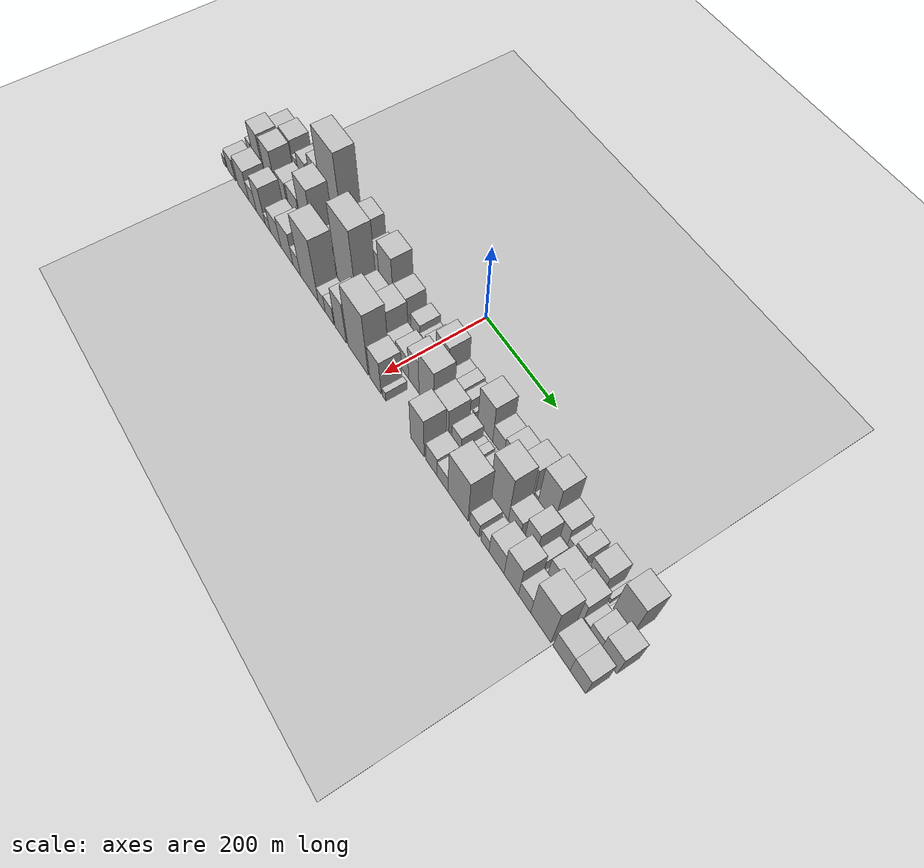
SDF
<?xml version="1.0" encoding="utf-8"?>

<sdf version="1.6">

   <world name="default">

      <gui fullscreen="0">

         <camera name="user_camera">

            <pose>-15 0 4.57585 0 0 0</pose>

            <view_controller>orbit</view_controller>

         </camera>

      </gui>

      <scene>

         <sky>

           <clouds>

             <speed>12</speed>

           </clouds>

         </sky>

         <ambient>0.4 0.4 0.4 1</ambient>

         <background>0.7 0.7 0.7 1</background>

         <shadows>1</shadows>

      </scene>

      <gravity>0 0 -9.8066</gravity>

      <magnetic_field>6e-06 2.3e-05 -4.2e-05</magnetic_field>

      <physics default="0" name="default_physics" type="ode">

         <ode>

            <solver>

               <type>quick</type>

               <iters>10</iters>

               <sor>1.0</sor>

               <use_dynamic_moi_rescaling>0</use_dynamic_moi_rescaling>

            </solver>

            <constraints>

               <cfm>0</cfm>

               <erp>0.2</erp>

               <contact_max_correcting_vel>100</contact_max_correcting_vel>

               <contact_surface_layer>0.001</contact_surface_layer>

            </constraints>

         </ode>

         <max_step_size>0.004</max_step_size>

         <real_time_factor>1</real_time_factor>

         <real_time_update_rate>250</real_time_update_rate>

      </physics>

      <light name="sun" type="directional">

         <cast_shadows>1</cast_shadows>

         <pose>0 0 10 0 0 0</pose>

         <diffuse>0.8 0.8 0.8 1</diffuse>

         <specular>0.2 0.2 0.2 1</specular>

         <attenuation>

            <range>1000</range>

            <constant>0.9</constant>

            <linear>0.01</linear>

            <quadratic>0.001</quadratic>

         </attenuation>

         <direction>-0.5 0.1 -0.9</direction>

      </light>

      <include>

         <name>ground_plane_1</name>

         <uri>model://HANNAS_ground_plane</uri>

         <pose>0 0 0  0 0 0</pose>

      </include>

      <include>

         <name>ground_plane_2</name>

         <uri>model://HANNAS_ground_plane</uri>

         <pose>100 0 0  0 0 0</pose>

      </include>

      <model name="building_1">

         <static>1</static>

         <pose frame="">100.0000 -531.4663 0 0.000000 0.000000 0.000000</pose>

         <link name="link">

            <pose frame="">0 0 30.00 0 0 0</pose>

            <collision name="collision">

               <geometry>

                  <box>

                     <size>40.0000 33.0674 60.0000</size>

                  </box>

               </geometry>

               <max_contacts>10</max_contacts>

               <surface>

                  <contact>

                     <ode/>

                  </contact>

                  <bounce/>

                  <friction>

                     <torsional>

                        <ode/>

                     </torsional>

                     <ode/>

                  </friction>

               </surface>

            </collision>

            <visual name="visual">

               <cast_shadows>0</cast_shadows>

               <geometry>

                  <box>

                     <size>40.0000 33.0674 60.0000</size>

                  </box>

               </geometry>

               <material>

                  <script>

                     <uri>model://HANNAS_wall/materials/scripts</uri>

                     <uri>model://HANNAS_wall/materials/textures</uri>

                     <name>vrc/HANNAS_wall</name>

                  </script>

               </material>

            </visual>

            <self_collide>0</self_collide>

            <enable_wind>0</enable_wind>

            <kinematic>0</kinematic>

         </link>

      </model>

      <model name="building_2">

         <static>1</static>

         <pose frame="">100.0000 -483.7740 0 0.000000 0.000000 0.000000</pose>

         <link name="link">

            <pose frame="">0 0 37.50 0 0 0</pose>

            <collision name="collision">

               <geometry>

                  <box>

                     <size>40.0000 42.3172 75.0000</size>

                  </box>

               </geometry>

               <max_contacts>10</max_contacts>

               <surface>

                  <contact>

                     <ode/>

                  </contact>

                  <bounce/>

                  <friction>

                     <torsional>

                        <ode/>

                     </torsional>

                     <ode/>

                  </friction>

               </surface>

            </collision>

            <visual name="visual">

               <cast_shadows>0</cast_shadows>

               <geometry>

                  <box>

                     <size>40.0000 42.3172 75.0000</size>

                  </box>

               </geometry>

               <material>

                  <script>

                     <uri>model://HANNAS_wall/materials/scripts</uri>

                     <uri>model://HANNAS_wall/materials/textures</uri>

                     <name>vrc/HANNAS_wall</name>

                  </script>

               </material>

            </visual>

            <self_collide>0</self_collide>

            <enable_wind>0</enable_wind>

            <kinematic>0</kinematic>

         </link>

      </model>

      <model name="building_3">

         <static>1</static>

         <pose frame="">100.0000 -452.2309 0 0.000000 0.000000 0.000000</pose>

         <link name="link">

            <pose frame="">0 0 19.50 0 0 0</pose>

            <collision name="collision">

               <geometry>

                  <box>

                     <size>40.0000 20.7689 39.0000</size>

                  </box>

               </geometry>

               <max_contacts>10</max_contacts>

               <surface>

                  <contact>

                     <ode/>

                  </contact>

                  <bounce/>

                  <friction>

                     <torsional>

                        <ode/>

                     </torsional>

                     <ode/>

                  </friction>

               </surface>

            </collision>

            <visual name="visual">

               <cast_shadows>0</cast_shadows>

               <geometry>

                  <box>

                     <size>40.0000 20.7689 39.0000</size>

                  </box>

               </geometry>

               <material>

                  <script>

                     <uri>model://HANNAS_wall/materials/scripts</uri>

                     <uri>model://HANNAS_wall/materials/textures</uri>

                     <name>vrc/HANNAS_wall</name>

                  </script>

               </material>

            </visual>

            <self_collide>0</self_collide>

            <enable_wind>0</enable_wind>

            <kinematic>0</kinematic>

         </link>

      </model>

      <model name="building_4">

         <static>1</static>

         <pose frame="">100.0000 -424.5817 0 0.000000 0.000000 0.000000</pose>

         <link name="link">

            <pose frame="">0 0 33.00 0 0 0</pose>

            <collision name="collision">

               <geometry>

                  <box>

                     <size>40.0000 34.5296 66.0000</size>

                  </box>

               </geometry>

               <max_contacts>10</max_contacts>

               <surface>

                  <contact>

                     <ode/>

                  </contact>

                  <bounce/>

                  <friction>

                     <torsional>

                        <ode/>

                     </torsional>

                     <ode/>

                  </friction>

               </surface>

            </collision>

            <visual name="visual">

               <cast_shadows>0</cast_shadows>

               <geometry>

                  <box>

                     <size>40.0000 34.5296 66.0000</size>

                  </box>

               </geometry>

               <material>

                  <script>

                     <uri>model://HANNAS_wall/materials/scripts</uri>

                     <uri>model://HANNAS_wall/materials/textures</uri>

                     <name>vrc/HANNAS_wall</name>

                  </script>

               </material>

            </visual>

            <self_collide>0</self_collide>

            <enable_wind>0</enable_wind>

            <kinematic>0</kinematic>

         </link>

      </model>

      <model name="building_5">

         <static>1</static>

         <pose frame="">100.0000 -398.8540 0 0.000000 0.000000 0.000000</pose>

         <link name="link">

            <pose frame="">0 0 15.00 0 0 0</pose>

            <collision name="collision">

               <geometry>

                  <box>

                     <size>40.0000 16.9257 30.0000</size>

                  </box>

               </geometry>

               <max_contacts>10</max_contacts>

               <surface>

                  <contact>

                     <ode/>

                  </contact>

                  <bounce/>

                  <friction>

                     <torsional>

                        <ode/>

                     </torsional>

                     <ode/>

                  </friction>

               </surface>

            </collision>

            <visual name="visual">

               <cast_shadows>0</cast_shadows>

               <geometry>

                  <box>

                     <size>40.0000 16.9257 30.0000</size>

                  </box>

               </geometry>

               <material>

                  <script>

                     <uri>model://HANNAS_wall/materials/scripts</uri>

                     <uri>model://HANNAS_wall/materials/textures</uri>

                     <name>vrc/HANNAS_wall</name>

                  </script>

               </material>

            </visual>

            <self_collide>0</self_collide>

            <enable_wind>0</enable_wind>

            <kinematic>0</kinematic>

         </link>

      </model>

      <model name="building_6">

         <static>1</static>

         <pose frame="">100.0000 -373.3653 0 0.000000 0.000000 0.000000</pose>

         <link name="link">

            <pose frame="">0 0 55.50 0 0 0</pose>

            <collision name="collision">

               <geometry>

                  <box>

                     <size>40.0000 34.0517 111.0000</size>

                  </box>

               </geometry>

               <max_contacts>10</max_contacts>

               <surface>

                  <contact>

                     <ode/>

                  </contact>

                  <bounce/>

                  <friction>

                     <torsional>

                        <ode/>

                     </torsional>

                     <ode/>

                  </friction>

               </surface>

            </collision>

            <visual name="visual">

               <cast_shadows>0</cast_shadows>

               <geometry>

                  <box>

                     <size>40.0000 34.0517 111.0000</size>

                  </box>

               </geometry>

               <material>

                  <script>

                     <uri>model://HANNAS_wall/materials/scripts</uri>

                     <uri>model://HANNAS_wall/materials/textures</uri>

                     <name>vrc/HANNAS_wall</name>

                  </script>

               </material>

            </visual>

            <self_collide>0</self_collide>

            <enable_wind>0</enable_wind>

            <kinematic>0</kinematic>

         </link>

      </model>

      <model name="building_7">

         <static>1</static>

         <pose frame="">100.0000 -312.9656 0 0.000000 0.000000 0.000000</pose>

         <link name="link">

            <pose frame="">0 0 109.50 0 0 0</pose>

            <collision name="collision">

               <geometry>

                  <box>

                     <size>40.0000 72.7477 219.0000</size>

                  </box>

               </geometry>

               <max_contacts>10</max_contacts>

               <surface>

                  <contact>

                     <ode/>

                  </contact>

                  <bounce/>

                  <friction>

                     <torsional>

                        <ode/>

                     </torsional>

                     <ode/>

                  </friction>

               </surface>

            </collision>

            <visual name="visual">

               <cast_shadows>0</cast_shadows>

               <geometry>

                  <box>

                     <size>40.0000 72.7477 219.0000</size>

                  </box>

               </geometry>

               <material>

                  <script>

                     <uri>model://HANNAS_wall/materials/scripts</uri>

                     <uri>model://HANNAS_wall/materials/textures</uri>

                     <name>vrc/HANNAS_wall</name>

                  </script>

               </material>

            </visual>

            <self_collide>0</self_collide>

            <enable_wind>0</enable_wind>

            <kinematic>0</kinematic>

         </link>

      </model>

      <model name="building_8">

         <static>1</static>

         <pose frame="">100.0000 -268.7394 0 0.000000 0.000000 0.000000</pose>

         <link name="link">

            <pose frame="">0 0 15.00 0 0 0</pose>

            <collision name="collision">

               <geometry>

                  <box>

                     <size>40.0000 15.7048 30.0000</size>

                  </box>

               </geometry>

               <max_contacts>10</max_contacts>

               <surface>

                  <contact>

                     <ode/>

                  </contact>

                  <bounce/>

                  <friction>

                     <torsional>

                        <ode/>

                     </torsional>

                     <ode/>

                  </friction>

               </surface>

            </collision>

            <visual name="visual">

               <cast_shadows>0</cast_shadows>

               <geometry>

                  <box>

                     <size>40.0000 15.7048 30.0000</size>

                  </box>

               </geometry>

               <material>

                  <script>

                     <uri>model://HANNAS_wall/materials/scripts</uri>

                     <uri>model://HANNAS_wall/materials/textures</uri>

                     <name>vrc/HANNAS_wall</name>

                  </script>

               </material>

            </visual>

            <self_collide>0</self_collide>

            <enable_wind>0</enable_wind>

            <kinematic>0</kinematic>

         </link>

      </model>

      <model name="building_9">

         <static>1</static>

         <pose frame="">100.0000 -246.7180 0 0.000000 0.000000 0.000000</pose>

         <link name="link">

            <pose frame="">0 0 24.00 0 0 0</pose>

            <collision name="collision">

               <geometry>

                  <box>

                     <size>40.0000 28.3378 48.0000</size>

                  </box>

               </geometry>

               <max_contacts>10</max_contacts>

               <surface>

                  <contact>

                     <ode/>

                  </contact>

                  <bounce/>

                  <friction>

                     <torsional>

                        <ode/>

                     </torsional>

                     <ode/>

                  </friction>

               </surface>

            </collision>

            <visual name="visual">

               <cast_shadows>0</cast_shadows>

               <geometry>

                  <box>

                     <size>40.0000 28.3378 48.0000</size>

                  </box>

               </geometry>

               <material>

                  <script>

                     <uri>model://HANNAS_wall/materials/scripts</uri>

                     <uri>model://HANNAS_wall/materials/textures</uri>

                     <name>vrc/HANNAS_wall</name>

                  </script>

               </material>

            </visual>

            <self_collide>0</self_collide>

            <enable_wind>0</enable_wind>

            <kinematic>0</kinematic>

         </link>

      </model>

      <model name="building_10">

         <static>1</static>

         <pose frame="">100.0000 -211.7277 0 0.000000 0.000000 0.000000</pose>

         <link name="link">

            <pose frame="">0 0 66.00 0 0 0</pose>

            <collision name="collision">

               <geometry>

                  <box>

                     <size>40.0000 41.6429 132.0000</size>

                  </box>

               </geometry>

               <max_contacts>10</max_contacts>

               <surface>

                  <contact>

                     <ode/>

                  </contact>

                  <bounce/>

                  <friction>

                     <torsional>

                        <ode/>

                     </torsional>

                     <ode/>

                  </friction>

               </surface>

            </collision>

            <visual name="visual">

               <cast_shadows>0</cast_shadows>

               <geometry>

                  <box>

                     <size>40.0000 41.6429 132.0000</size>

                  </box>

               </geometry>

               <material>

                  <script>

                     <uri>model://HANNAS_wall/materials/scripts</uri>

                     <uri>model://HANNAS_wall/materials/textures</uri>

                     <name>vrc/HANNAS_wall</name>

                  </script>

               </material>

            </visual>

            <self_collide>0</self_collide>

            <enable_wind>0</enable_wind>

            <kinematic>0</kinematic>

         </link>

      </model>

      <model name="building_11">

         <static>1</static>

         <pose frame="">100.0000 -165.4333 0 0.000000 0.000000 0.000000</pose>

         <link name="link">

            <pose frame="">0 0 46.50 0 0 0</pose>

            <collision name="collision">

               <geometry>

                  <box>

                     <size>40.0000 32.9459 93.0000</size>

                  </box>

               </geometry>

               <max_contacts>10</max_contacts>

               <surface>

                  <contact>

                     <ode/>

                  </contact>

                  <bounce/>

                  <friction>

                     <torsional>

                        <ode/>

                     </torsional>

                     <ode/>

                  </friction>

               </surface>

            </collision>

            <visual name="visual">

               <cast_shadows>0</cast_shadows>

               <geometry>

                  <box>

                     <size>40.0000 32.9459 93.0000</size>

                  </box>

               </geometry>

               <material>

                  <script>

                     <uri>model://HANNAS_wall/materials/scripts</uri>

                     <uri>model://HANNAS_wall/materials/textures</uri>

                     <name>vrc/HANNAS_wall</name>

                  </script>

               </material>

            </visual>

            <self_collide>0</self_collide>

            <enable_wind>0</enable_wind>

            <kinematic>0</kinematic>

         </link>

      </model>

      <model name="building_12">

         <static>1</static>

         <pose frame="">100.0000 -126.4425 0 0.000000 0.000000 0.000000</pose>

         <link name="link">

            <pose frame="">0 0 67.50 0 0 0</pose>

            <collision name="collision">

               <geometry>

                  <box>

                     <size>40.0000 45.0357 135.0000</size>

                  </box>

               </geometry>

               <max_contacts>10</max_contacts>

               <surface>

                  <contact>

                     <ode/>

                  </contact>

                  <bounce/>

                  <friction>

                     <torsional>

                        <ode/>

                     </torsional>

                     <ode/>

                  </friction>

               </surface>

            </collision>

            <visual name="visual">

               <cast_shadows>0</cast_shadows>

               <geometry>

                  <box>

                     <size>40.0000 45.0357 135.0000</size>

                  </box>

               </geometry>

               <material>

                  <script>

                     <uri>model://HANNAS_wall/materials/scripts</uri>

                     <uri>model://HANNAS_wall/materials/textures</uri>

                     <name>vrc/HANNAS_wall</name>

                  </script>

               </material>

            </visual>

            <self_collide>0</self_collide>

            <enable_wind>0</enable_wind>

            <kinematic>0</kinematic>

         </link>

      </model>

      <model name="building_13">

         <static>1</static>

         <pose frame="">100.0000 -82.1082 0 0.000000 0.000000 0.000000</pose>

         <link name="link">

            <pose frame="">0 0 36.00 0 0 0</pose>

            <collision name="collision">

               <geometry>

                  <box>

                     <size>40.0000 37.6330 72.0000</size>

                  </box>

               </geometry>

               <max_contacts>10</max_contacts>

               <surface>

                  <contact>

                     <ode/>

                  </contact>

                  <bounce/>

                  <friction>

                     <torsional>

                        <ode/>

                     </torsional>

                     <ode/>

                  </friction>

               </surface>

            </collision>

            <visual name="visual">

               <cast_shadows>0</cast_shadows>

               <geometry>

                  <box>

                     <size>40.0000 37.6330 72.0000</size>

                  </box>

               </geometry>

               <material>

                  <script>

                     <uri>model://HANNAS_wall/materials/scripts</uri>

                     <uri>model://HANNAS_wall/materials/textures</uri>

                     <name>vrc/HANNAS_wall</name>

                  </script>

               </material>

            </visual>

            <self_collide>0</self_collide>

            <enable_wind>0</enable_wind>

            <kinematic>0</kinematic>

         </link>

      </model>

      <model name="building_14">

         <static>1</static>

         <pose frame="">100.0000 -51.2164 0 0.000000 0.000000 0.000000</pose>

         <link name="link">

            <pose frame="">0 0 7.50 0 0 0</pose>

            <collision name="collision">

               <geometry>

                  <box>

                     <size>40.0000 6.1504 15.0000</size>

                  </box>

               </geometry>

               <max_contacts>10</max_contacts>

               <surface>

                  <contact>

                     <ode/>

                  </contact>

                  <bounce/>

                  <friction>

                     <torsional>

                        <ode/>

                     </torsional>

                     <ode/>

                  </friction>

               </surface>

            </collision>

            <visual name="visual">

               <cast_shadows>0</cast_shadows>

               <geometry>

                  <box>

                     <size>40.0000 6.1504 15.0000</size>

                  </box>

               </geometry>

               <material>

                  <script>

                     <uri>model://HANNAS_wall/materials/scripts</uri>

                     <uri>model://HANNAS_wall/materials/textures</uri>

                     <name>vrc/HANNAS_wall</name>

                  </script>

               </material>

            </visual>

            <self_collide>0</self_collide>

            <enable_wind>0</enable_wind>

            <kinematic>0</kinematic>

         </link>

      </model>

      <model name="building_15">

         <static>1</static>

         <pose frame="">100.0000 -33.5812 0 0.000000 0.000000 0.000000</pose>

         <link name="link">

            <pose frame="">0 0 25.50 0 0 0</pose>

            <collision name="collision">

               <geometry>

                  <box>

                     <size>40.0000 29.1201 51.0000</size>

                  </box>

               </geometry>

               <max_contacts>10</max_contacts>

               <surface>

                  <contact>

                     <ode/>

                  </contact>

                  <bounce/>

                  <friction>

                     <torsional>

                        <ode/>

                     </torsional>

                     <ode/>

                  </friction>

               </surface>

            </collision>

            <visual name="visual">

               <cast_shadows>0</cast_shadows>

               <geometry>

                  <box>

                     <size>40.0000 29.1201 51.0000</size>

                  </box>

               </geometry>

               <material>

                  <script>

                     <uri>model://HANNAS_wall/materials/scripts</uri>

                     <uri>model://HANNAS_wall/materials/textures</uri>

                     <name>vrc/HANNAS_wall</name>

                  </script>

               </material>

            </visual>

            <self_collide>0</self_collide>

            <enable_wind>0</enable_wind>

            <kinematic>0</kinematic>

         </link>

      </model>

      <model name="building_16">

         <static>1</static>

         <pose frame="">100.0000 -11.0467 0 0.000000 0.000000 0.000000</pose>

         <link name="link">

            <pose frame="">0 0 15.00 0 0 0</pose>

            <collision name="collision">

               <geometry>

                  <box>

                     <size>40.0000 15.9488 30.0000</size>

                  </box>

               </geometry>

               <max_contacts>10</max_contacts>

               <surface>

                  <contact>

                     <ode/>

                  </contact>

                  <bounce/>

                  <friction>

                     <torsional>

                        <ode/>

                     </torsional>

                     <ode/>

                  </friction>

               </surface>

            </collision>

            <visual name="visual">

               <cast_shadows>0</cast_shadows>

               <geometry>

                  <box>

                     <size>40.0000 15.9488 30.0000</size>

                  </box>

               </geometry>

               <material>

                  <script>

                     <uri>model://HANNAS_wall/materials/scripts</uri>

                     <uri>model://HANNAS_wall/materials/textures</uri>

                     <name>vrc/HANNAS_wall</name>

                  </script>

               </material>

            </visual>

            <self_collide>0</self_collide>

            <enable_wind>0</enable_wind>

            <kinematic>0</kinematic>

         </link>

      </model>

      <model name="building_17">

         <static>1</static>

         <pose frame="">100.0000 9.3485 0 0.000000 0.000000 0.000000</pose>

         <link name="link">

            <pose frame="">0 0 22.50 0 0 0</pose>

            <collision name="collision">

               <geometry>

                  <box>

                     <size>40.0000 24.8416 45.0000</size>

                  </box>

               </geometry>

               <max_contacts>10</max_contacts>

               <surface>

                  <contact>

                     <ode/>

                  </contact>

                  <bounce/>

                  <friction>

                     <torsional>

                        <ode/>

                     </torsional>

                     <ode/>

                  </friction>

               </surface>

            </collision>

            <visual name="visual">

               <cast_shadows>0</cast_shadows>

               <geometry>

                  <box>

                     <size>40.0000 24.8416 45.0000</size>

                  </box>

               </geometry>

               <material>

                  <script>

                     <uri>model://HANNAS_wall/materials/scripts</uri>

                     <uri>model://HANNAS_wall/materials/textures</uri>

                     <name>vrc/HANNAS_wall</name>

                  </script>

               </material>

            </visual>

            <self_collide>0</self_collide>

            <enable_wind>0</enable_wind>

            <kinematic>0</kinematic>

         </link>

      </model>

      <model name="building_18">

         <static>1</static>

         <pose frame="">100.0000 49.2545 0 0.000000 0.000000 0.000000</pose>

         <link name="link">

            <pose frame="">0 0 52.50 0 0 0</pose>

            <collision name="collision">

               <geometry>

                  <box>

                     <size>40.0000 38.9705 105.0000</size>

                  </box>

               </geometry>

               <max_contacts>10</max_contacts>

               <surface>

                  <contact>

                     <ode/>

                  </contact>

                  <bounce/>

                  <friction>

                     <torsional>

                        <ode/>

                     </torsional>

                     <ode/>

                  </friction>

               </surface>

            </collision>

            <visual name="visual">

               <cast_shadows>0</cast_shadows>

               <geometry>

                  <box>

                     <size>40.0000 38.9705 105.0000</size>

                  </box>

               </geometry>

               <material>

                  <script>

                     <uri>model://HANNAS_wall/materials/scripts</uri>

                     <uri>model://HANNAS_wall/materials/textures</uri>

                     <name>vrc/HANNAS_wall</name>

                  </script>

               </material>

            </visual>

            <self_collide>0</self_collide>

            <enable_wind>0</enable_wind>

            <kinematic>0</kinematic>

         </link>

      </model>

      <model name="building_19">

         <static>1</static>

         <pose frame="">100.0000 79.6568 0 0.000000 0.000000 0.000000</pose>

         <link name="link">

            <pose frame="">0 0 19.50 0 0 0</pose>

            <collision name="collision">

               <geometry>

                  <box>

                     <size>40.0000 21.8342 39.0000</size>

                  </box>

               </geometry>

               <max_contacts>10</max_contacts>

               <surface>

                  <contact>

                     <ode/>

                  </contact>

                  <bounce/>

                  <friction>

                     <torsional>

                        <ode/>

                     </torsional>

                     <ode/>

                  </friction>

               </surface>

            </collision>

            <visual name="visual">

               <cast_shadows>0</cast_shadows>

               <geometry>

                  <box>

                     <size>40.0000 21.8342 39.0000</size>

                  </box>

               </geometry>

               <material>

                  <script>

                     <uri>model://HANNAS_wall/materials/scripts</uri>

                     <uri>model://HANNAS_wall/materials/textures</uri>

                     <name>vrc/HANNAS_wall</name>

                  </script>

               </material>

            </visual>

            <self_collide>0</self_collide>

            <enable_wind>0</enable_wind>

            <kinematic>0</kinematic>

         </link>

      </model>

      <model name="building_20">

         <static>1</static>

         <pose frame="">100.0000 101.7693 0 0.000000 0.000000 0.000000</pose>

         <link name="link">

            <pose frame="">0 0 21.00 0 0 0</pose>

            <collision name="collision">

               <geometry>

                  <box>

                     <size>40.0000 22.3909 42.0000</size>

                  </box>

               </geometry>

               <max_contacts>10</max_contacts>

               <surface>

                  <contact>

                     <ode/>

                  </contact>

                  <bounce/>

                  <friction>

                     <torsional>

                        <ode/>

                     </torsional>

                     <ode/>

                  </friction>

               </surface>

            </collision>

            <visual name="visual">

               <cast_shadows>0</cast_shadows>

               <geometry>

                  <box>

                     <size>40.0000 22.3909 42.0000</size>

                  </box>

               </geometry>

               <material>

                  <script>

                     <uri>model://HANNAS_wall/materials/scripts</uri>

                     <uri>model://HANNAS_wall/materials/textures</uri>

                     <name>vrc/HANNAS_wall</name>

                  </script>

               </material>

            </visual>

            <self_collide>0</self_collide>

            <enable_wind>0</enable_wind>

            <kinematic>0</kinematic>

         </link>

      </model>

      <model name="building_21">

         <static>1</static>

         <pose frame="">100.0000 122.1437 0 0.000000 0.000000 0.000000</pose>

         <link name="link">

            <pose frame="">0 0 16.50 0 0 0</pose>

            <collision name="collision">

               <geometry>

                  <box>

                     <size>40.0000 18.3578 33.0000</size>

                  </box>

               </geometry>

               <max_contacts>10</max_contacts>

               <surface>

                  <contact>

                     <ode/>

                  </contact>

                  <bounce/>

                  <friction>

                     <torsional>

                        <ode/>

                     </torsional>

                     <ode/>

                  </friction>

               </surface>

            </collision>

            <visual name="visual">

               <cast_shadows>0</cast_shadows>

               <geometry>

                  <box>

                     <size>40.0000 18.3578 33.0000</size>

                  </box>

               </geometry>

               <material>

                  <script>

                     <uri>model://HANNAS_wall/materials/scripts</uri>

                     <uri>model://HANNAS_wall/materials/textures</uri>

                     <name>vrc/HANNAS_wall</name>

                  </script>

               </material>

            </visual>

            <self_collide>0</self_collide>

            <enable_wind>0</enable_wind>

            <kinematic>0</kinematic>

         </link>

      </model>

      <model name="building_22">

         <static>1</static>

         <pose frame="">100.0000 142.0112 0 0.000000 0.000000 0.000000</pose>

         <link name="link">

            <pose frame="">0 0 9.00 0 0 0</pose>

            <collision name="collision">

               <geometry>

                  <box>

                     <size>40.0000 7.3772 18.0000</size>

                  </box>

               </geometry>

               <max_contacts>10</max_contacts>

               <surface>

                  <contact>

                     <ode/>

                  </contact>

                  <bounce/>

                  <friction>

                     <torsional>

                        <ode/>

                     </torsional>

                     <ode/>

                  </friction>

               </surface>

            </collision>

            <visual name="visual">

               <cast_shadows>0</cast_shadows>

               <geometry>

                  <box>

                     <size>40.0000 7.3772 18.0000</size>

                  </box>

               </geometry>

               <material>

                  <script>

                     <uri>model://HANNAS_wall/materials/scripts</uri>

                     <uri>model://HANNAS_wall/materials/textures</uri>

                     <name>vrc/HANNAS_wall</name>

                  </script>

               </material>

            </visual>

            <self_collide>0</self_collide>

            <enable_wind>0</enable_wind>

            <kinematic>0</kinematic>

         </link>

      </model>

      <model name="building_23">

         <static>1</static>

         <pose frame="">100.0000 174.6972 0 0.000000 0.000000 0.000000</pose>

         <link name="link">

            <pose frame="">0 0 57.00 0 0 0</pose>

            <collision name="collision">

               <geometry>

                  <box>

                     <size>40.0000 41.9947 114.0000</size>

                  </box>

               </geometry>

               <max_contacts>10</max_contacts>

               <surface>

                  <contact>

                     <ode/>

                  </contact>

                  <bounce/>

                  <friction>

                     <torsional>

                        <ode/>

                     </torsional>

                     <ode/>

                  </friction>

               </surface>

            </collision>

            <visual name="visual">

               <cast_shadows>0</cast_shadows>

               <geometry>

                  <box>

                     <size>40.0000 41.9947 114.0000</size>

                  </box>

               </geometry>

               <material>

                  <script>

                     <uri>model://HANNAS_wall/materials/scripts</uri>

                     <uri>model://HANNAS_wall/materials/textures</uri>

                     <name>vrc/HANNAS_wall</name>

                  </script>

               </material>

            </visual>

            <self_collide>0</self_collide>

            <enable_wind>0</enable_wind>

            <kinematic>0</kinematic>

         </link>

      </model>

      <model name="building_24">

         <static>1</static>

         <pose frame="">100.0000 211.2063 0 0.000000 0.000000 0.000000</pose>

         <link name="link">

            <pose frame="">0 0 30.00 0 0 0</pose>

            <collision name="collision">

               <geometry>

                  <box>

                     <size>40.0000 31.0236 60.0000</size>

                  </box>

               </geometry>

               <max_contacts>10</max_contacts>

               <surface>

                  <contact>

                     <ode/>

                  </contact>

                  <bounce/>

                  <friction>

                     <torsional>

                        <ode/>

                     </torsional>

                     <ode/>

                  </friction>

               </surface>

            </collision>

            <visual name="visual">

               <cast_shadows>0</cast_shadows>

               <geometry>

                  <box>

                     <size>40.0000 31.0236 60.0000</size>

                  </box>

               </geometry>

               <material>

                  <script>

                     <uri>model://HANNAS_wall/materials/scripts</uri>

                     <uri>model://HANNAS_wall/materials/textures</uri>

                     <name>vrc/HANNAS_wall</name>

                  </script>

               </material>

            </visual>

            <self_collide>0</self_collide>

            <enable_wind>0</enable_wind>

            <kinematic>0</kinematic>

         </link>

      </model>

      <model name="building_25">

         <static>1</static>

         <pose frame="">100.0000 245.6507 0 0.000000 0.000000 0.000000</pose>

         <link name="link">

            <pose frame="">0 0 34.50 0 0 0</pose>

            <collision name="collision">

               <geometry>

                  <box>

                     <size>40.0000 37.8653 69.0000</size>

                  </box>

               </geometry>

               <max_contacts>10</max_contacts>

               <surface>

                  <contact>

                     <ode/>

                  </contact>

                  <bounce/>

                  <friction>

                     <torsional>

                        <ode/>

                     </torsional>

                     <ode/>

                  </friction>

               </surface>

            </collision>

            <visual name="visual">

               <cast_shadows>0</cast_shadows>

               <geometry>

                  <box>

                     <size>40.0000 37.8653 69.0000</size>

                  </box>

               </geometry>

               <material>

                  <script>

                     <uri>model://HANNAS_wall/materials/scripts</uri>

                     <uri>model://HANNAS_wall/materials/textures</uri>

                     <name>vrc/HANNAS_wall</name>

                  </script>

               </material>

            </visual>

            <self_collide>0</self_collide>

            <enable_wind>0</enable_wind>

            <kinematic>0</kinematic>

         </link>

      </model>

      <model name="building_26">

         <static>1</static>

         <pose frame="">100.0000 288.7055 0 0.000000 0.000000 0.000000</pose>

         <link name="link">

            <pose frame="">0 0 51.00 0 0 0</pose>

            <collision name="collision">

               <geometry>

                  <box>

                     <size>40.0000 36.2443 102.0000</size>

                  </box>

               </geometry>

               <max_contacts>10</max_contacts>

               <surface>

                  <contact>

                     <ode/>

                  </contact>

                  <bounce/>

                  <friction>

                     <torsional>

                        <ode/>

                     </torsional>

                     <ode/>

                  </friction>

               </surface>

            </collision>

            <visual name="visual">

               <cast_shadows>0</cast_shadows>

               <geometry>

                  <box>

                     <size>40.0000 36.2443 102.0000</size>

                  </box>

               </geometry>

               <material>

                  <script>

                     <uri>model://HANNAS_wall/materials/scripts</uri>

                     <uri>model://HANNAS_wall/materials/textures</uri>

                     <name>vrc/HANNAS_wall</name>

                  </script>

               </material>

            </visual>

            <self_collide>0</self_collide>

            <enable_wind>0</enable_wind>

            <kinematic>0</kinematic>

         </link>

      </model>

      <model name="building_27">

         <static>1</static>

         <pose frame="">100.0000 311.8651 0 0.000000 0.000000 0.000000</pose>

         <link name="link">

            <pose frame="">0 0 12.00 0 0 0</pose>

            <collision name="collision">

               <geometry>

                  <box>

                     <size>40.0000 10.0750 24.0000</size>

                  </box>

               </geometry>

               <max_contacts>10</max_contacts>

               <surface>

                  <contact>

                     <ode/>

                  </contact>

                  <bounce/>

                  <friction>

                     <torsional>

                        <ode/>

                     </torsional>

                     <ode/>

                  </friction>

               </surface>

            </collision>

            <visual name="visual">

               <cast_shadows>0</cast_shadows>

               <geometry>

                  <box>

                     <size>40.0000 10.0750 24.0000</size>

                  </box>

               </geometry>

               <material>

                  <script>

                     <uri>model://HANNAS_wall/materials/scripts</uri>

                     <uri>model://HANNAS_wall/materials/textures</uri>

                     <name>vrc/HANNAS_wall</name>

                  </script>

               </material>

            </visual>

            <self_collide>0</self_collide>

            <enable_wind>0</enable_wind>

            <kinematic>0</kinematic>

         </link>

      </model>

      <model name="building_28">

         <static>1</static>

         <pose frame="">100.0000 337.6767 0 0.000000 0.000000 0.000000</pose>

         <link name="link">

            <pose frame="">0 0 67.50 0 0 0</pose>

            <collision name="collision">

               <geometry>

                  <box>

                     <size>40.0000 41.5482 135.0000</size>

                  </box>

               </geometry>

               <max_contacts>10</max_contacts>

               <surface>

                  <contact>

                     <ode/>

                  </contact>

                  <bounce/>

                  <friction>

                     <torsional>

                        <ode/>

                     </torsional>

                     <ode/>

                  </friction>

               </surface>

            </collision>

            <visual name="visual">

               <cast_shadows>0</cast_shadows>

               <geometry>

                  <box>

                     <size>40.0000 41.5482 135.0000</size>

                  </box>

               </geometry>

               <material>

                  <script>

                     <uri>model://HANNAS_wall/materials/scripts</uri>

                     <uri>model://HANNAS_wall/materials/textures</uri>

                     <name>vrc/HANNAS_wall</name>

                  </script>

               </material>

            </visual>

            <self_collide>0</self_collide>

            <enable_wind>0</enable_wind>

            <kinematic>0</kinematic>

         </link>

      </model>

      <model name="building_29">

         <static>1</static>

         <pose frame="">100.0000 375.9420 0 0.000000 0.000000 0.000000</pose>

         <link name="link">

            <pose frame="">0 0 30.00 0 0 0</pose>

            <collision name="collision">

               <geometry>

                  <box>

                     <size>40.0000 34.9823 60.0000</size>

                  </box>

               </geometry>

               <max_contacts>10</max_contacts>

               <surface>

                  <contact>

                     <ode/>

                  </contact>

                  <bounce/>

                  <friction>

                     <torsional>

                        <ode/>

                     </torsional>

                     <ode/>

                  </friction>

               </surface>

            </collision>

            <visual name="visual">

               <cast_shadows>0</cast_shadows>

               <geometry>

                  <box>

                     <size>40.0000 34.9823 60.0000</size>

                  </box>

               </geometry>

               <material>

                  <script>

                     <uri>model://HANNAS_wall/materials/scripts</uri>

                     <uri>model://HANNAS_wall/materials/textures</uri>

                     <name>vrc/HANNAS_wall</name>

                  </script>

               </material>

            </visual>

            <self_collide>0</self_collide>

            <enable_wind>0</enable_wind>

            <kinematic>0</kinematic>

         </link>

      </model>

      <model name="building_30">

         <static>1</static>

         <pose frame="">100.0000 401.3811 0 0.000000 0.000000 0.000000</pose>

         <link name="link">

            <pose frame="">0 0 15.00 0 0 0</pose>

            <collision name="collision">

               <geometry>

                  <box>

                     <size>40.0000 15.8960 30.0000</size>

                  </box>

               </geometry>

               <max_contacts>10</max_contacts>

               <surface>

                  <contact>

                     <ode/>

                  </contact>

                  <bounce/>

                  <friction>

                     <torsional>

                        <ode/>

                     </torsional>

                     <ode/>

                  </friction>

               </surface>

            </collision>

            <visual name="visual">

               <cast_shadows>0</cast_shadows>

               <geometry>

                  <box>

                     <size>40.0000 15.8960 30.0000</size>

                  </box>

               </geometry>

               <material>

                  <script>

                     <uri>model://HANNAS_wall/materials/scripts</uri>

                     <uri>model://HANNAS_wall/materials/textures</uri>

                     <name>vrc/HANNAS_wall</name>

                  </script>

               </material>

            </visual>

            <self_collide>0</self_collide>

            <enable_wind>0</enable_wind>

            <kinematic>0</kinematic>

         </link>

      </model>

      <model name="building_31">

         <static>1</static>

         <pose frame="">100.0000 421.6672 0 0.000000 0.000000 0.000000</pose>

         <link name="link">

            <pose frame="">0 0 24.00 0 0 0</pose>

            <collision name="collision">

               <geometry>

                  <box>

                     <size>40.0000 24.6762 48.0000</size>

                  </box>

               </geometry>

               <max_contacts>10</max_contacts>

               <surface>

                  <contact>

                     <ode/>

                  </contact>

                  <bounce/>

                  <friction>

                     <torsional>

                        <ode/>

                     </torsional>

                     <ode/>

                  </friction>

               </surface>

            </collision>

            <visual name="visual">

               <cast_shadows>0</cast_shadows>

               <geometry>

                  <box>

                     <size>40.0000 24.6762 48.0000</size>

                  </box>

               </geometry>

               <material>

                  <script>

                     <uri>model://HANNAS_wall/materials/scripts</uri>

                     <uri>model://HANNAS_wall/materials/textures</uri>

                     <name>vrc/HANNAS_wall</name>

                  </script>

               </material>

            </visual>

            <self_collide>0</self_collide>

            <enable_wind>0</enable_wind>

            <kinematic>0</kinematic>

         </link>

      </model>

      <model name="building_32">

         <static>1</static>

         <pose frame="">100.0000 461.3938 0 0.000000 0.000000 0.000000</pose>

         <link name="link">

            <pose frame="">0 0 34.50 0 0 0</pose>

            <collision name="collision">

               <geometry>

                  <box>

                     <size>40.0000 36.7770 69.0000</size>

                  </box>

               </geometry>

               <max_contacts>10</max_contacts>

               <surface>

                  <contact>

                     <ode/>

                  </contact>

                  <bounce/>

                  <friction>

                     <torsional>

                        <ode/>

                     </torsional>

                     <ode/>

                  </friction>

               </surface>

            </collision>

            <visual name="visual">

               <cast_shadows>0</cast_shadows>

               <geometry>

                  <box>

                     <size>40.0000 36.7770 69.0000</size>

                  </box>

               </geometry>

               <material>

                  <script>

                     <uri>model://HANNAS_wall/materials/scripts</uri>

                     <uri>model://HANNAS_wall/materials/textures</uri>

                     <name>vrc/HANNAS_wall</name>

                  </script>

               </material>

            </visual>

            <self_collide>0</self_collide>

            <enable_wind>0</enable_wind>

            <kinematic>0</kinematic>

         </link>

      </model>

      <model name="building_33">

         <static>1</static>

         <pose frame="">100.0000 492.0627 0 0.000000 0.000000 0.000000</pose>

         <link name="link">

            <pose frame="">0 0 9.00 0 0 0</pose>

            <collision name="collision">

               <geometry>

                  <box>

                     <size>40.0000 8.5607 18.0000</size>

                  </box>

               </geometry>

               <max_contacts>10</max_contacts>

               <surface>

                  <contact>

                     <ode/>

                  </contact>

                  <bounce/>

                  <friction>

                     <torsional>

                        <ode/>

                     </torsional>

                     <ode/>

                  </friction>

               </surface>

            </collision>

            <visual name="visual">

               <cast_shadows>0</cast_shadows>

               <geometry>

                  <box>

                     <size>40.0000 8.5607 18.0000</size>

                  </box>

               </geometry>

               <material>

                  <script>

                     <uri>model://HANNAS_wall/materials/scripts</uri>

                     <uri>model://HANNAS_wall/materials/textures</uri>

                     <name>vrc/HANNAS_wall</name>

                  </script>

               </material>

            </visual>

            <self_collide>0</self_collide>

            <enable_wind>0</enable_wind>

            <kinematic>0</kinematic>

         </link>

      </model>

      <model name="building_34">

         <static>1</static>

         <pose frame="">100.0000 526.4093 0 0.000000 0.000000 0.000000</pose>

         <link name="link">

            <pose frame="">0 0 58.50 0 0 0</pose>

            <collision name="collision">

               <geometry>

                  <box>

                     <size>40.0000 44.1324 117.0000</size>

                  </box>

               </geometry>

               <max_contacts>10</max_contacts>

               <surface>

                  <contact>

                     <ode/>

                  </contact>

                  <bounce/>

                  <friction>

                     <torsional>

                        <ode/>

                     </torsional>

                     <ode/>

                  </friction>

               </surface>

            </collision>

            <visual name="visual">

               <cast_shadows>0</cast_shadows>

               <geometry>

                  <box>

                     <size>40.0000 44.1324 117.0000</size>

                  </box>

               </geometry>

               <material>

                  <script>

                     <uri>model://HANNAS_wall/materials/scripts</uri>

                     <uri>model://HANNAS_wall/materials/textures</uri>

                     <name>vrc/HANNAS_wall</name>

                  </script>

               </material>

            </visual>

            <self_collide>0</self_collide>

            <enable_wind>0</enable_wind>

            <kinematic>0</kinematic>

         </link>

      </model>

      <model name="building_35">

         <static>1</static>

         <pose frame="">152.0000 -538.6052 0 0.000000 0.000000 0.000000</pose>

         <link name="link">

            <pose frame="">0 0 18.00 0 0 0</pose>

            <collision name="collision">

               <geometry>

                  <box>

                     <size>40.0000 18.7897 36.0000</size>

                  </box>

               </geometry>

               <max_contacts>10</max_contacts>

               <surface>

                  <contact>

                     <ode/>

                  </contact>

                  <bounce/>

                  <friction>

                     <torsional>

                        <ode/>

                     </torsional>

                     <ode/>

                  </friction>

               </surface>

            </collision>

            <visual name="visual">

               <cast_shadows>0</cast_shadows>

               <geometry>

                  <box>

                     <size>40.0000 18.7897 36.0000</size>

                  </box>

               </geometry>

               <material>

                  <script>

                     <uri>model://HANNAS_wall/materials/scripts</uri>

                     <uri>model://HANNAS_wall/materials/textures</uri>

                     <name>vrc/HANNAS_wall</name>

                  </script>

               </material>

            </visual>

            <self_collide>0</self_collide>

            <enable_wind>0</enable_wind>

            <kinematic>0</kinematic>

         </link>

      </model>

      <model name="building_36">

         <static>1</static>

         <pose frame="">152.0000 -502.4161 0 0.000000 0.000000 0.000000</pose>

         <link name="link">

            <pose frame="">0 0 51.00 0 0 0</pose>

            <collision name="collision">

               <geometry>

                  <box>

                     <size>40.0000 39.5884 102.0000</size>

                  </box>

               </geometry>

               <max_contacts>10</max_contacts>

               <surface>

                  <contact>

                     <ode/>

                  </contact>

                  <bounce/>

                  <friction>

                     <torsional>

                        <ode/>

                     </torsional>

                     <ode/>

                  </friction>

               </surface>

            </collision>

            <visual name="visual">

               <cast_shadows>0</cast_shadows>

               <geometry>

                  <box>

                     <size>40.0000 39.5884 102.0000</size>

                  </box>

               </geometry>

               <material>

                  <script>

                     <uri>model://HANNAS_wall/materials/scripts</uri>

                     <uri>model://HANNAS_wall/materials/textures</uri>

                     <name>vrc/HANNAS_wall</name>

                  </script>

               </material>

            </visual>

            <self_collide>0</self_collide>

            <enable_wind>0</enable_wind>

            <kinematic>0</kinematic>

         </link>

      </model>

      <model name="building_37">

         <static>1</static>

         <pose frame="">152.0000 -453.9032 0 0.000000 0.000000 0.000000</pose>

         <link name="link">

            <pose frame="">0 0 52.50 0 0 0</pose>

            <collision name="collision">

               <geometry>

                  <box>

                     <size>40.0000 41.4374 105.0000</size>

                  </box>

               </geometry>

               <max_contacts>10</max_contacts>

               <surface>

                  <contact>

                     <ode/>

                  </contact>

                  <bounce/>

                  <friction>

                     <torsional>

                        <ode/>

                     </torsional>

                     <ode/>

                  </friction>

               </surface>

            </collision>

            <visual name="visual">

               <cast_shadows>0</cast_shadows>

               <geometry>

                  <box>

                     <size>40.0000 41.4374 105.0000</size>

                  </box>

               </geometry>

               <material>

                  <script>

                     <uri>model://HANNAS_wall/materials/scripts</uri>

                     <uri>model://HANNAS_wall/materials/textures</uri>

                     <name>vrc/HANNAS_wall</name>

                  </script>

               </material>

            </visual>

            <self_collide>0</self_collide>

            <enable_wind>0</enable_wind>

            <kinematic>0</kinematic>

         </link>

      </model>

      <model name="building_38">

         <static>1</static>

         <pose frame="">152.0000 -405.3885 0 0.000000 0.000000 0.000000</pose>

         <link name="link">

            <pose frame="">0 0 33.00 0 0 0</pose>

            <collision name="collision">

               <geometry>

                  <box>

                     <size>40.0000 35.5921 66.0000</size>

                  </box>

               </geometry>

               <max_contacts>10</max_contacts>

               <surface>

                  <contact>

                     <ode/>

                  </contact>

                  <bounce/>

                  <friction>

                     <torsional>

                        <ode/>

                     </torsional>

                     <ode/>

                  </friction>

               </surface>

            </collision>

            <visual name="visual">

               <cast_shadows>0</cast_shadows>

               <geometry>

                  <box>

                     <size>40.0000 35.5921 66.0000</size>

                  </box>

               </geometry>

               <material>

                  <script>

                     <uri>model://HANNAS_wall/materials/scripts</uri>

                     <uri>model://HANNAS_wall/materials/textures</uri>

                     <name>vrc/HANNAS_wall</name>

                  </script>

               </material>

            </visual>

            <self_collide>0</self_collide>

            <enable_wind>0</enable_wind>

            <kinematic>0</kinematic>

         </link>

      </model>

      <model name="building_39">

         <static>1</static>

         <pose frame="">152.0000 -359.5633 0 0.000000 0.000000 0.000000</pose>

         <link name="link">

            <pose frame="">0 0 37.50 0 0 0</pose>

            <collision name="collision">

               <geometry>

                  <box>

                     <size>40.0000 42.0581 75.0000</size>

                  </box>

               </geometry>

               <max_contacts>10</max_contacts>

               <surface>

                  <contact>

                     <ode/>

                  </contact>

                  <bounce/>

                  <friction>

                     <torsional>

                        <ode/>

                     </torsional>

                     <ode/>

                  </friction>

               </surface>

            </collision>

            <visual name="visual">

               <cast_shadows>0</cast_shadows>

               <geometry>

                  <box>

                     <size>40.0000 42.0581 75.0000</size>

                  </box>

               </geometry>

               <material>

                  <script>

                     <uri>model://HANNAS_wall/materials/scripts</uri>

                     <uri>model://HANNAS_wall/materials/textures</uri>

                     <name>vrc/HANNAS_wall</name>

                  </script>

               </material>

            </visual>

            <self_collide>0</self_collide>

            <enable_wind>0</enable_wind>

            <kinematic>0</kinematic>

         </link>

      </model>

      <model name="building_40">

         <static>1</static>

         <pose frame="">152.0000 -310.0447 0 0.000000 0.000000 0.000000</pose>

         <link name="link">

            <pose frame="">0 0 75.00 0 0 0</pose>

            <collision name="collision">

               <geometry>

                  <box>

                     <size>40.0000 46.9792 150.0000</size>

                  </box>

               </geometry>

               <max_contacts>10</max_contacts>

               <surface>

                  <contact>

                     <ode/>

                  </contact>

                  <bounce/>

                  <friction>

                     <torsional>

                        <ode/>

                     </torsional>

                     <ode/>

                  </friction>

               </surface>

            </collision>

            <visual name="visual">

               <cast_shadows>0</cast_shadows>

               <geometry>

                  <box>

                     <size>40.0000 46.9792 150.0000</size>

                  </box>

               </geometry>

               <material>

                  <script>

                     <uri>model://HANNAS_wall/materials/scripts</uri>

                     <uri>model://HANNAS_wall/materials/textures</uri>

                     <name>vrc/HANNAS_wall</name>

                  </script>

               </material>

            </visual>

            <self_collide>0</self_collide>

            <enable_wind>0</enable_wind>

            <kinematic>0</kinematic>

         </link>

      </model>

      <model name="building_41">

         <static>1</static>

         <pose frame="">152.0000 -275.4106 0 0.000000 0.000000 0.000000</pose>

         <link name="link">

            <pose frame="">0 0 19.50 0 0 0</pose>

            <collision name="collision">

               <geometry>

                  <box>

                     <size>40.0000 22.2889 39.0000</size>

                  </box>

               </geometry>

               <max_contacts>10</max_contacts>

               <surface>

                  <contact>

                     <ode/>

                  </contact>

                  <bounce/>

                  <friction>

                     <torsional>

                        <ode/>

                     </torsional>

                     <ode/>

                  </friction>

               </surface>

            </collision>

            <visual name="visual">

               <cast_shadows>0</cast_shadows>

               <geometry>

                  <box>

                     <size>40.0000 22.2889 39.0000</size>

                  </box>

               </geometry>

               <material>

                  <script>

                     <uri>model://HANNAS_wall/materials/scripts</uri>

                     <uri>model://HANNAS_wall/materials/textures</uri>

                     <name>vrc/HANNAS_wall</name>

                  </script>

               </material>

            </visual>

            <self_collide>0</self_collide>

            <enable_wind>0</enable_wind>

            <kinematic>0</kinematic>

         </link>

      </model>

      <model name="building_42">

         <static>1</static>

         <pose frame="">152.0000 -250.4712 0 0.000000 0.000000 0.000000</pose>

         <link name="link">

            <pose frame="">0 0 24.00 0 0 0</pose>

            <collision name="collision">

               <geometry>

                  <box>

                     <size>40.0000 27.5900 48.0000</size>

                  </box>

               </geometry>

               <max_contacts>10</max_contacts>

               <surface>

                  <contact>

                     <ode/>

                  </contact>

                  <bounce/>

                  <friction>

                     <torsional>

                        <ode/>

                     </torsional>

                     <ode/>

                  </friction>

               </surface>

            </collision>

            <visual name="visual">

               <cast_shadows>0</cast_shadows>

               <geometry>

                  <box>

                     <size>40.0000 27.5900 48.0000</size>

                  </box>

               </geometry>

               <material>

                  <script>

                     <uri>model://HANNAS_wall/materials/scripts</uri>

                     <uri>model://HANNAS_wall/materials/textures</uri>

                     <name>vrc/HANNAS_wall</name>

                  </script>

               </material>

            </visual>

            <self_collide>0</self_collide>

            <enable_wind>0</enable_wind>

            <kinematic>0</kinematic>

         </link>

      </model>

      <model name="building_43">

         <static>1</static>

         <pose frame="">152.0000 -221.2421 0 0.000000 0.000000 0.000000</pose>

         <link name="link">

            <pose frame="">0 0 16.50 0 0 0</pose>

            <collision name="collision">

               <geometry>

                  <box>

                     <size>40.0000 18.8682 33.0000</size>

                  </box>

               </geometry>

               <max_contacts>10</max_contacts>

               <surface>

                  <contact>

                     <ode/>

                  </contact>

                  <bounce/>

                  <friction>

                     <torsional>

                        <ode/>

                     </torsional>

                     <ode/>

                  </friction>

               </surface>

            </collision>

            <visual name="visual">

               <cast_shadows>0</cast_shadows>

               <geometry>

                  <box>

                     <size>40.0000 18.8682 33.0000</size>

                  </box>

               </geometry>

               <material>

                  <script>

                     <uri>model://HANNAS_wall/materials/scripts</uri>

                     <uri>model://HANNAS_wall/materials/textures</uri>

                     <name>vrc/HANNAS_wall</name>

                  </script>

               </material>

            </visual>

            <self_collide>0</self_collide>

            <enable_wind>0</enable_wind>

            <kinematic>0</kinematic>

         </link>

      </model>

      <model name="building_44">

         <static>1</static>

         <pose frame="">152.0000 -171.8982 0 0.000000 0.000000 0.000000</pose>

         <link name="link">

            <pose frame="">0 0 103.50 0 0 0</pose>

            <collision name="collision">

               <geometry>

                  <box>

                     <size>40.0000 67.8195 207.0000</size>

                  </box>

               </geometry>

               <max_contacts>10</max_contacts>

               <surface>

                  <contact>

                     <ode/>

                  </contact>

                  <bounce/>

                  <friction>

                     <torsional>

                        <ode/>

                     </torsional>

                     <ode/>

                  </friction>

               </surface>

            </collision>

            <visual name="visual">

               <cast_shadows>0</cast_shadows>

               <geometry>

                  <box>

                     <size>40.0000 67.8195 207.0000</size>

                  </box>

               </geometry>

               <material>

                  <script>

                     <uri>model://HANNAS_wall/materials/scripts</uri>

                     <uri>model://HANNAS_wall/materials/textures</uri>

                     <name>vrc/HANNAS_wall</name>

                  </script>

               </material>

            </visual>

            <self_collide>0</self_collide>

            <enable_wind>0</enable_wind>

            <kinematic>0</kinematic>

         </link>

      </model>

      <model name="building_45">

         <static>1</static>

         <pose frame="">152.0000 -104.2163 0 0.000000 0.000000 0.000000</pose>

         <link name="link">

            <pose frame="">0 0 43.50 0 0 0</pose>

            <collision name="collision">

               <geometry>

                  <box>

                     <size>40.0000 51.5444 87.0000</size>

                  </box>

               </geometry>

               <max_contacts>10</max_contacts>

               <surface>

                  <contact>

                     <ode/>

                  </contact>

                  <bounce/>

                  <friction>

                     <torsional>

                        <ode/>

                     </torsional>

                     <ode/>

                  </friction>

               </surface>

            </collision>

            <visual name="visual">

               <cast_shadows>0</cast_shadows>

               <geometry>

                  <box>

                     <size>40.0000 51.5444 87.0000</size>

                  </box>

               </geometry>

               <material>

                  <script>

                     <uri>model://HANNAS_wall/materials/scripts</uri>

                     <uri>model://HANNAS_wall/materials/textures</uri>

                     <name>vrc/HANNAS_wall</name>

                  </script>

               </material>

            </visual>

            <self_collide>0</self_collide>

            <enable_wind>0</enable_wind>

            <kinematic>0</kinematic>

         </link>

      </model>

      <model name="building_46">

         <static>1</static>

         <pose frame="">152.0000 -57.3280 0 0.000000 0.000000 0.000000</pose>

         <link name="link">

            <pose frame="">0 0 55.50 0 0 0</pose>

            <collision name="collision">

               <geometry>

                  <box>

                     <size>40.0000 42.2322 111.0000</size>

                  </box>

               </geometry>

               <max_contacts>10</max_contacts>

               <surface>

                  <contact>

                     <ode/>

                  </contact>

                  <bounce/>

                  <friction>

                     <torsional>

                        <ode/>

                     </torsional>

                     <ode/>

                  </friction>

               </surface>

            </collision>

            <visual name="visual">

               <cast_shadows>0</cast_shadows>

               <geometry>

                  <box>

                     <size>40.0000 42.2322 111.0000</size>

                  </box>

               </geometry>

               <material>

                  <script>

                     <uri>model://HANNAS_wall/materials/scripts</uri>

                     <uri>model://HANNAS_wall/materials/textures</uri>

                     <name>vrc/HANNAS_wall</name>

                  </script>

               </material>

            </visual>

            <self_collide>0</self_collide>

            <enable_wind>0</enable_wind>

            <kinematic>0</kinematic>

         </link>

      </model>

      <model name="building_47">

         <static>1</static>

         <pose frame="">152.0000 -22.6772 0 0.000000 0.000000 0.000000</pose>

         <link name="link">

            <pose frame="">0 0 25.50 0 0 0</pose>

            <collision name="collision">

               <geometry>

                  <box>

                     <size>40.0000 27.0694 51.0000</size>

                  </box>

               </geometry>

               <max_contacts>10</max_contacts>

               <surface>

                  <contact>

                     <ode/>

                  </contact>

                  <bounce/>

                  <friction>

                     <torsional>

                        <ode/>

                     </torsional>

                     <ode/>

                  </friction>

               </surface>

            </collision>

            <visual name="visual">

               <cast_shadows>0</cast_shadows>

               <geometry>

                  <box>

                     <size>40.0000 27.0694 51.0000</size>

                  </box>

               </geometry>

               <material>

                  <script>

                     <uri>model://HANNAS_wall/materials/scripts</uri>

                     <uri>model://HANNAS_wall/materials/textures</uri>

                     <name>vrc/HANNAS_wall</name>

                  </script>

               </material>

            </visual>

            <self_collide>0</self_collide>

            <enable_wind>0</enable_wind>

            <kinematic>0</kinematic>

         </link>

      </model>

      <model name="building_48">

         <static>1</static>

         <pose frame="">152.0000 10.2735 0 0.000000 0.000000 0.000000</pose>

         <link name="link">

            <pose frame="">0 0 33.00 0 0 0</pose>

            <collision name="collision">

               <geometry>

                  <box>

                     <size>40.0000 38.8319 66.0000</size>

                  </box>

               </geometry>

               <max_contacts>10</max_contacts>

               <surface>

                  <contact>

                     <ode/>

                  </contact>

                  <bounce/>

                  <friction>

                     <torsional>

                        <ode/>

                     </torsional>

                     <ode/>

                  </friction>

               </surface>

            </collision>

            <visual name="visual">

               <cast_shadows>0</cast_shadows>

               <geometry>

                  <box>

                     <size>40.0000 38.8319 66.0000</size>

                  </box>

               </geometry>

               <material>

                  <script>

                     <uri>model://HANNAS_wall/materials/scripts</uri>

                     <uri>model://HANNAS_wall/materials/textures</uri>

                     <name>vrc/HANNAS_wall</name>

                  </script>

               </material>

            </visual>

            <self_collide>0</self_collide>

            <enable_wind>0</enable_wind>

            <kinematic>0</kinematic>

         </link>

      </model>

      <model name="building_49">

         <static>1</static>

         <pose frame="">152.0000 45.5225 0 0.000000 0.000000 0.000000</pose>

         <link name="link">

            <pose frame="">0 0 51.00 0 0 0</pose>

            <collision name="collision">

               <geometry>

                  <box>

                     <size>40.0000 31.6661 102.0000</size>

                  </box>

               </geometry>

               <max_contacts>10</max_contacts>

               <surface>

                  <contact>

                     <ode/>

                  </contact>

                  <bounce/>

                  <friction>

                     <torsional>

                        <ode/>

                     </torsional>

                     <ode/>

                  </friction>

               </surface>

            </collision>

            <visual name="visual">

               <cast_shadows>0</cast_shadows>

               <geometry>

                  <box>

                     <size>40.0000 31.6661 102.0000</size>

                  </box>

               </geometry>

               <material>

                  <script>

                     <uri>model://HANNAS_wall/materials/scripts</uri>

                     <uri>model://HANNAS_wall/materials/textures</uri>

                     <name>vrc/HANNAS_wall</name>

                  </script>

               </material>

            </visual>

            <self_collide>0</self_collide>

            <enable_wind>0</enable_wind>

            <kinematic>0</kinematic>

         </link>

      </model>

      <model name="building_50">

         <static>1</static>

         <pose frame="">152.0000 83.6295 0 0.000000 0.000000 0.000000</pose>

         <link name="link">

            <pose frame="">0 0 66.00 0 0 0</pose>

            <collision name="collision">

               <geometry>

                  <box>

                     <size>40.0000 44.5480 132.0000</size>

                  </box>

               </geometry>

               <max_contacts>10</max_contacts>

               <surface>

                  <contact>

                     <ode/>

                  </contact>

                  <bounce/>

                  <friction>

                     <torsional>

                        <ode/>

                     </torsional>

                     <ode/>

                  </friction>

               </surface>

            </collision>

            <visual name="visual">

               <cast_shadows>0</cast_shadows>

               <geometry>

                  <box>

                     <size>40.0000 44.5480 132.0000</size>

                  </box>

               </geometry>

               <material>

                  <script>

                     <uri>model://HANNAS_wall/materials/scripts</uri>

                     <uri>model://HANNAS_wall/materials/textures</uri>

                     <name>vrc/HANNAS_wall</name>

                  </script>

               </material>

            </visual>

            <self_collide>0</self_collide>

            <enable_wind>0</enable_wind>

            <kinematic>0</kinematic>

         </link>

      </model>

      <model name="building_51">

         <static>1</static>

         <pose frame="">152.0000 127.2248 0 0.000000 0.000000 0.000000</pose>

         <link name="link">

            <pose frame="">0 0 40.50 0 0 0</pose>

            <collision name="collision">

               <geometry>

                  <box>

                     <size>40.0000 42.6425 81.0000</size>

                  </box>

               </geometry>

               <max_contacts>10</max_contacts>

               <surface>

                  <contact>

                     <ode/>

                  </contact>

                  <bounce/>

                  <friction>

                     <torsional>

                        <ode/>

                     </torsional>

                     <ode/>

                  </friction>

               </surface>

            </collision>

            <visual name="visual">

               <cast_shadows>0</cast_shadows>

               <geometry>

                  <box>

                     <size>40.0000 42.6425 81.0000</size>

                  </box>

               </geometry>

               <material>

                  <script>

                     <uri>model://HANNAS_wall/materials/scripts</uri>

                     <uri>model://HANNAS_wall/materials/textures</uri>

                     <name>vrc/HANNAS_wall</name>

                  </script>

               </material>

            </visual>

            <self_collide>0</self_collide>

            <enable_wind>0</enable_wind>

            <kinematic>0</kinematic>

         </link>

      </model>

      <model name="building_52">

         <static>1</static>

         <pose frame="">152.0000 171.4712 0 0.000000 0.000000 0.000000</pose>

         <link name="link">

            <pose frame="">0 0 25.50 0 0 0</pose>

            <collision name="collision">

               <geometry>

                  <box>

                     <size>40.0000 27.8504 51.0000</size>

                  </box>

               </geometry>

               <max_contacts>10</max_contacts>

               <surface>

                  <contact>

                     <ode/>

                  </contact>

                  <bounce/>

                  <friction>

                     <torsional>

                        <ode/>

                     </torsional>

                     <ode/>

                  </friction>

               </surface>

            </collision>

            <visual name="visual">

               <cast_shadows>0</cast_shadows>

               <geometry>

                  <box>

                     <size>40.0000 27.8504 51.0000</size>

                  </box>

               </geometry>

               <material>

                  <script>

                     <uri>model://HANNAS_wall/materials/scripts</uri>

                     <uri>model://HANNAS_wall/materials/textures</uri>

                     <name>vrc/HANNAS_wall</name>

                  </script>

               </material>

            </visual>

            <self_collide>0</self_collide>

            <enable_wind>0</enable_wind>

            <kinematic>0</kinematic>

         </link>

      </model>

      <model name="building_53">

         <static>1</static>

         <pose frame="">152.0000 195.6565 0 0.000000 0.000000 0.000000</pose>

         <link name="link">

            <pose frame="">0 0 13.50 0 0 0</pose>

            <collision name="collision">

               <geometry>

                  <box>

                     <size>40.0000 12.5201 27.0000</size>

                  </box>

               </geometry>

               <max_contacts>10</max_contacts>

               <surface>

                  <contact>

                     <ode/>

                  </contact>

                  <bounce/>

                  <friction>

                     <torsional>

                        <ode/>

                     </torsional>

                     <ode/>

                  </friction>

               </surface>

            </collision>

            <visual name="visual">

               <cast_shadows>0</cast_shadows>

               <geometry>

                  <box>

                     <size>40.0000 12.5201 27.0000</size>

                  </box>

               </geometry>

               <material>

                  <script>

                     <uri>model://HANNAS_wall/materials/scripts</uri>

                     <uri>model://HANNAS_wall/materials/textures</uri>

                     <name>vrc/HANNAS_wall</name>

                  </script>

               </material>

            </visual>

            <self_collide>0</self_collide>

            <enable_wind>0</enable_wind>

            <kinematic>0</kinematic>

         </link>

      </model>

      <model name="building_54">

         <static>1</static>

         <pose frame="">152.0000 209.7513 0 0.000000 0.000000 0.000000</pose>

         <link name="link">

            <pose frame="">0 0 15.00 0 0 0</pose>

            <collision name="collision">

               <geometry>

                  <box>

                     <size>40.0000 15.6696 30.0000</size>

                  </box>

               </geometry>

               <max_contacts>10</max_contacts>

               <surface>

                  <contact>

                     <ode/>

                  </contact>

                  <bounce/>

                  <friction>

                     <torsional>

                        <ode/>

                     </torsional>

                     <ode/>

                  </friction>

               </surface>

            </collision>

            <visual name="visual">

               <cast_shadows>0</cast_shadows>

               <geometry>

                  <box>

                     <size>40.0000 15.6696 30.0000</size>

                  </box>

               </geometry>

               <material>

                  <script>

                     <uri>model://HANNAS_wall/materials/scripts</uri>

                     <uri>model://HANNAS_wall/materials/textures</uri>

                     <name>vrc/HANNAS_wall</name>

                  </script>

               </material>

            </visual>

            <self_collide>0</self_collide>

            <enable_wind>0</enable_wind>

            <kinematic>0</kinematic>

         </link>

      </model>

      <model name="building_55">

         <static>1</static>

         <pose frame="">152.0000 238.0543 0 0.000000 0.000000 0.000000</pose>

         <link name="link">

            <pose frame="">0 0 21.00 0 0 0</pose>

            <collision name="collision">

               <geometry>

                  <box>

                     <size>40.0000 24.9364 42.0000</size>

                  </box>

               </geometry>

               <max_contacts>10</max_contacts>

               <surface>

                  <contact>

                     <ode/>

                  </contact>

                  <bounce/>

                  <friction>

                     <torsional>

                        <ode/>

                     </torsional>

                     <ode/>

                  </friction>

               </surface>

            </collision>

            <visual name="visual">

               <cast_shadows>0</cast_shadows>

               <geometry>

                  <box>

                     <size>40.0000 24.9364 42.0000</size>

                  </box>

               </geometry>

               <material>

                  <script>

                     <uri>model://HANNAS_wall/materials/scripts</uri>

                     <uri>model://HANNAS_wall/materials/textures</uri>

                     <name>vrc/HANNAS_wall</name>

                  </script>

               </material>

            </visual>

            <self_collide>0</self_collide>

            <enable_wind>0</enable_wind>

            <kinematic>0</kinematic>

         </link>

      </model>

      <model name="building_56">

         <static>1</static>

         <pose frame="">152.0000 255.4384 0 0.000000 0.000000 0.000000</pose>

         <link name="link">

            <pose frame="">0 0 10.50 0 0 0</pose>

            <collision name="collision">

               <geometry>

                  <box>

                     <size>40.0000 9.8317 21.0000</size>

                  </box>

               </geometry>

               <max_contacts>10</max_contacts>

               <surface>

                  <contact>

                     <ode/>

                  </contact>

                  <bounce/>

                  <friction>

                     <torsional>

                        <ode/>

                     </torsional>

                     <ode/>

                  </friction>

               </surface>

            </collision>

            <visual name="visual">

               <cast_shadows>0</cast_shadows>

               <geometry>

                  <box>

                     <size>40.0000 9.8317 21.0000</size>

                  </box>

               </geometry>

               <material>

                  <script>

                     <uri>model://HANNAS_wall/materials/scripts</uri>

                     <uri>model://HANNAS_wall/materials/textures</uri>

                     <name>vrc/HANNAS_wall</name>

                  </script>

               </material>

            </visual>

            <self_collide>0</self_collide>

            <enable_wind>0</enable_wind>

            <kinematic>0</kinematic>

         </link>

      </model>

      <model name="building_57">

         <static>1</static>

         <pose frame="">152.0000 290.1492 0 0.000000 0.000000 0.000000</pose>

         <link name="link">

            <pose frame="">0 0 75.00 0 0 0</pose>

            <collision name="collision">

               <geometry>

                  <box>

                     <size>40.0000 49.5898 150.0000</size>

                  </box>

               </geometry>

               <max_contacts>10</max_contacts>

               <surface>

                  <contact>

                     <ode/>

                  </contact>

                  <bounce/>

                  <friction>

                     <torsional>

                        <ode/>

                     </torsional>

                     <ode/>

                  </friction>

               </surface>

            </collision>

            <visual name="visual">

               <cast_shadows>0</cast_shadows>

               <geometry>

                  <box>

                     <size>40.0000 49.5898 150.0000</size>

                  </box>

               </geometry>

               <material>

                  <script>

                     <uri>model://HANNAS_wall/materials/scripts</uri>

                     <uri>model://HANNAS_wall/materials/textures</uri>

                     <name>vrc/HANNAS_wall</name>

                  </script>

               </material>

            </visual>

            <self_collide>0</self_collide>

            <enable_wind>0</enable_wind>

            <kinematic>0</kinematic>

         </link>

      </model>

      <model name="building_58">

         <static>1</static>

         <pose frame="">152.0000 330.6442 0 0.000000 0.000000 0.000000</pose>

         <link name="link">

            <pose frame="">0 0 27.00 0 0 0</pose>

            <collision name="collision">

               <geometry>

                  <box>

                     <size>40.0000 31.4003 54.0000</size>

                  </box>

               </geometry>

               <max_contacts>10</max_contacts>

               <surface>

                  <contact>

                     <ode/>

                  </contact>

                  <bounce/>

                  <friction>

                     <torsional>

                        <ode/>

                     </torsional>

                     <ode/>

                  </friction>

               </surface>

            </collision>

            <visual name="visual">

               <cast_shadows>0</cast_shadows>

               <geometry>

                  <box>

                     <size>40.0000 31.4003 54.0000</size>

                  </box>

               </geometry>

               <material>

                  <script>

                     <uri>model://HANNAS_wall/materials/scripts</uri>

                     <uri>model://HANNAS_wall/materials/textures</uri>

                     <name>vrc/HANNAS_wall</name>

                  </script>

               </material>

            </visual>

            <self_collide>0</self_collide>

            <enable_wind>0</enable_wind>

            <kinematic>0</kinematic>

         </link>

      </model>

      <model name="building_59">

         <static>1</static>

         <pose frame="">152.0000 370.3391 0 0.000000 0.000000 0.000000</pose>

         <link name="link">

            <pose frame="">0 0 48.00 0 0 0</pose>

            <collision name="collision">

               <geometry>

                  <box>

                     <size>40.0000 29.9894 96.0000</size>

                  </box>

               </geometry>

               <max_contacts>10</max_contacts>

               <surface>

                  <contact>

                     <ode/>

                  </contact>

                  <bounce/>

                  <friction>

                     <torsional>

                        <ode/>

                     </torsional>

                     <ode/>

                  </friction>

               </surface>

            </collision>

            <visual name="visual">

               <cast_shadows>0</cast_shadows>

               <geometry>

                  <box>

                     <size>40.0000 29.9894 96.0000</size>

                  </box>

               </geometry>

               <material>

                  <script>

                     <uri>model://HANNAS_wall/materials/scripts</uri>

                     <uri>model://HANNAS_wall/materials/textures</uri>

                     <name>vrc/HANNAS_wall</name>

                  </script>

               </material>

            </visual>

            <self_collide>0</self_collide>

            <enable_wind>0</enable_wind>

            <kinematic>0</kinematic>

         </link>

      </model>

      <model name="building_60">

         <static>1</static>

         <pose frame="">152.0000 396.1795 0 0.000000 0.000000 0.000000</pose>

         <link name="link">

            <pose frame="">0 0 19.50 0 0 0</pose>

            <collision name="collision">

               <geometry>

                  <box>

                     <size>40.0000 21.6916 39.0000</size>

                  </box>

               </geometry>

               <max_contacts>10</max_contacts>

               <surface>

                  <contact>

                     <ode/>

                  </contact>

                  <bounce/>

                  <friction>

                     <torsional>

                        <ode/>

                     </torsional>

                     <ode/>

                  </friction>

               </surface>

            </collision>

            <visual name="visual">

               <cast_shadows>0</cast_shadows>

               <geometry>

                  <box>

                     <size>40.0000 21.6916 39.0000</size>

                  </box>

               </geometry>

               <material>

                  <script>

                     <uri>model://HANNAS_wall/materials/scripts</uri>

                     <uri>model://HANNAS_wall/materials/textures</uri>

                     <name>vrc/HANNAS_wall</name>

                  </script>

               </material>

            </visual>

            <self_collide>0</self_collide>

            <enable_wind>0</enable_wind>

            <kinematic>0</kinematic>

         </link>

      </model>

      <model name="building_61">

         <static>1</static>

         <pose frame="">152.0000 436.1327 0 0.000000 0.000000 0.000000</pose>

         <link name="link">

            <pose frame="">0 0 36.00 0 0 0</pose>

            <collision name="collision">

               <geometry>

                  <box>

                     <size>40.0000 42.2148 72.0000</size>

                  </box>

               </geometry>

               <max_contacts>10</max_contacts>

               <surface>

                  <contact>

                     <ode/>

                  </contact>

                  <bounce/>

                  <friction>

                     <torsional>

                        <ode/>

                     </torsional>

                     <ode/>

                  </friction>

               </surface>

            </collision>

            <visual name="visual">

               <cast_shadows>0</cast_shadows>

               <geometry>

                  <box>

                     <size>40.0000 42.2148 72.0000</size>

                  </box>

               </geometry>

               <material>

                  <script>

                     <uri>model://HANNAS_wall/materials/scripts</uri>

                     <uri>model://HANNAS_wall/materials/textures</uri>

                     <name>vrc/HANNAS_wall</name>

                  </script>

               </material>

            </visual>

            <self_collide>0</self_collide>

            <enable_wind>0</enable_wind>

            <kinematic>0</kinematic>

         </link>

      </model>

      <model name="building_62">

         <static>1</static>

         <pose frame="">152.0000 477.6932 0 0.000000 0.000000 0.000000</pose>

         <link name="link">

            <pose frame="">0 0 40.50 0 0 0</pose>

            <collision name="collision">

               <geometry>

                  <box>

                     <size>40.0000 40.9060 81.0000</size>

                  </box>

               </geometry>

               <max_contacts>10</max_contacts>

               <surface>

                  <contact>

                     <ode/>

                  </contact>

                  <bounce/>

                  <friction>

                     <torsional>

                        <ode/>

                     </torsional>

                     <ode/>

                  </friction>

               </surface>

            </collision>

            <visual name="visual">

               <cast_shadows>0</cast_shadows>

               <geometry>

                  <box>

                     <size>40.0000 40.9060 81.0000</size>

                  </box>

               </geometry>

               <material>

                  <script>

                     <uri>model://HANNAS_wall/materials/scripts</uri>

                     <uri>model://HANNAS_wall/materials/textures</uri>

                     <name>vrc/HANNAS_wall</name>

                  </script>

               </material>

            </visual>

            <self_collide>0</self_collide>

            <enable_wind>0</enable_wind>

            <kinematic>0</kinematic>

         </link>

      </model>

      <model name="building_63">

         <static>1</static>

         <pose frame="">152.0000 505.9911 0 0.000000 0.000000 0.000000</pose>

         <link name="link">

            <pose frame="">0 0 15.00 0 0 0</pose>

            <collision name="collision">

               <geometry>

                  <box>

                     <size>40.0000 15.6899 30.0000</size>

                  </box>

               </geometry>

               <max_contacts>10</max_contacts>

               <surface>

                  <contact>

                     <ode/>

                  </contact>

                  <bounce/>

                  <friction>

                     <torsional>

                        <ode/>

                     </torsional>

                     <ode/>

                  </friction>

               </surface>

            </collision>

            <visual name="visual">

               <cast_shadows>0</cast_shadows>

               <geometry>

                  <box>

                     <size>40.0000 15.6899 30.0000</size>

                  </box>

               </geometry>

               <material>

                  <script>

                     <uri>model://HANNAS_wall/materials/scripts</uri>

                     <uri>model://HANNAS_wall/materials/textures</uri>

                     <name>vrc/HANNAS_wall</name>

                  </script>

               </material>

            </visual>

            <self_collide>0</self_collide>

            <enable_wind>0</enable_wind>

            <kinematic>0</kinematic>

         </link>

      </model>

      <model name="building_64">

         <static>1</static>

         <pose frame="">152.0000 527.8593 0 0.000000 0.000000 0.000000</pose>

         <link name="link">

            <pose frame="">0 0 25.50 0 0 0</pose>

            <collision name="collision">

               <geometry>

                  <box>

                     <size>40.0000 28.0464 51.0000</size>

                  </box>

               </geometry>

               <max_contacts>10</max_contacts>

               <surface>

                  <contact>

                     <ode/>

                  </contact>

                  <bounce/>

                  <friction>

                     <torsional>

                        <ode/>

                     </torsional>

                     <ode/>

                  </friction>

               </surface>

            </collision>

            <visual name="visual">

               <cast_shadows>0</cast_shadows>

               <geometry>

                  <box>

                     <size>40.0000 28.0464 51.0000</size>

                  </box>

               </geometry>

               <material>

                  <script>

                     <uri>model://HANNAS_wall/materials/scripts</uri>

                     <uri>model://HANNAS_wall/materials/textures</uri>

                     <name>vrc/HANNAS_wall</name>

                  </script>

               </material>

            </visual>

            <self_collide>0</self_collide>

            <enable_wind>0</enable_wind>

            <kinematic>0</kinematic>

         </link>

      </model>

      <model name="building_65">

         <static>1</static>

         <pose frame="">152.0000 560.7917 0 0.000000 0.000000 0.000000</pose>

         <link name="link">

            <pose frame="">0 0 37.50 0 0 0</pose>

            <collision name="collision">

               <geometry>

                  <box>

                     <size>40.0000 37.8184 75.0000</size>

                  </box>

               </geometry>

               <max_contacts>10</max_contacts>

               <surface>

                  <contact>

                     <ode/>

                  </contact>

                  <bounce/>

                  <friction>

                     <torsional>

                        <ode/>

                     </torsional>

                     <ode/>

                  </friction>

               </surface>

            </collision>

            <visual name="visual">

               <cast_shadows>0</cast_shadows>

               <geometry>

                  <box>

                     <size>40.0000 37.8184 75.0000</size>

                  </box>

               </geometry>

               <material>

                  <script>

                     <uri>model://HANNAS_wall/materials/scripts</uri>

                     <uri>model://HANNAS_wall/materials/textures</uri>

                     <name>vrc/HANNAS_wall</name>

                  </script>

               </material>

            </visual>

            <self_collide>0</self_collide>

            <enable_wind>0</enable_wind>

            <kinematic>0</kinematic>

         </link>

      </model>

      <model name="building_66">

         <static>1</static>

         <pose frame="">204.0000 -537.8265 0 0.000000 0.000000 0.000000</pose>

         <link name="link">

            <pose frame="">0 0 13.50 0 0 0</pose>

            <collision name="collision">

               <geometry>

                  <box>

                     <size>40.0000 12.3471 27.0000</size>

                  </box>

               </geometry>

               <max_contacts>10</max_contacts>

               <surface>

                  <contact>

                     <ode/>

                  </contact>

                  <bounce/>

                  <friction>

                     <torsional>

                        <ode/>

                     </torsional>

                     <ode/>

                  </friction>

               </surface>

            </collision>

            <visual name="visual">

               <cast_shadows>0</cast_shadows>

               <geometry>

                  <box>

                     <size>40.0000 12.3471 27.0000</size>

                  </box>

               </geometry>

               <material>

                  <script>

                     <uri>model://HANNAS_wall/materials/scripts</uri>

                     <uri>model://HANNAS_wall/materials/textures</uri>

                     <name>vrc/HANNAS_wall</name>

                  </script>

               </material>

            </visual>

            <self_collide>0</self_collide>

            <enable_wind>0</enable_wind>

            <kinematic>0</kinematic>

         </link>

      </model>

      <model name="building_67">

         <static>1</static>

         <pose frame="">204.0000 -509.7639 0 0.000000 0.000000 0.000000</pose>

         <link name="link">

            <pose frame="">0 0 28.50 0 0 0</pose>

            <collision name="collision">

               <geometry>

                  <box>

                     <size>40.0000 31.7780 57.0000</size>

                  </box>

               </geometry>

               <max_contacts>10</max_contacts>

               <surface>

                  <contact>

                     <ode/>

                  </contact>

                  <bounce/>

                  <friction>

                     <torsional>

                        <ode/>

                     </torsional>

                     <ode/>

                  </friction>

               </surface>

            </collision>

            <visual name="visual">

               <cast_shadows>0</cast_shadows>

               <geometry>

                  <box>

                     <size>40.0000 31.7780 57.0000</size>

                  </box>

               </geometry>

               <material>

                  <script>

                     <uri>model://HANNAS_wall/materials/scripts</uri>

                     <uri>model://HANNAS_wall/materials/textures</uri>

                     <name>vrc/HANNAS_wall</name>

                  </script>

               </material>

            </visual>

            <self_collide>0</self_collide>

            <enable_wind>0</enable_wind>

            <kinematic>0</kinematic>

         </link>

      </model>

      <model name="building_68">

         <static>1</static>

         <pose frame="">204.0000 -461.7228 0 0.000000 0.000000 0.000000</pose>

         <link name="link">

            <pose frame="">0 0 39.00 0 0 0</pose>

            <collision name="collision">

               <geometry>

                  <box>

                     <size>40.0000 44.3043 78.0000</size>

                  </box>

               </geometry>

               <max_contacts>10</max_contacts>

               <surface>

                  <contact>

                     <ode/>

                  </contact>

                  <bounce/>

                  <friction>

                     <torsional>

                        <ode/>

                     </torsional>

                     <ode/>

                  </friction>

               </surface>

            </collision>

            <visual name="visual">

               <cast_shadows>0</cast_shadows>

               <geometry>

                  <box>

                     <size>40.0000 44.3043 78.0000</size>

                  </box>

               </geometry>

               <material>

                  <script>

                     <uri>model://HANNAS_wall/materials/scripts</uri>

                     <uri>model://HANNAS_wall/materials/textures</uri>

                     <name>vrc/HANNAS_wall</name>

                  </script>

               </material>

            </visual>

            <self_collide>0</self_collide>

            <enable_wind>0</enable_wind>

            <kinematic>0</kinematic>

         </link>

      </model>

      <model name="building_69">

         <static>1</static>

         <pose frame="">204.0000 -424.3368 0 0.000000 0.000000 0.000000</pose>

         <link name="link">

            <pose frame="">0 0 27.00 0 0 0</pose>

            <collision name="collision">

               <geometry>

                  <box>

                     <size>40.0000 30.4676 54.0000</size>

                  </box>

               </geometry>

               <max_contacts>10</max_contacts>

               <surface>

                  <contact>

                     <ode/>

                  </contact>

                  <bounce/>

                  <friction>

                     <torsional>

                        <ode/>

                     </torsional>

                     <ode/>

                  </friction>

               </surface>

            </collision>

            <visual name="visual">

               <cast_shadows>0</cast_shadows>

               <geometry>

                  <box>

                     <size>40.0000 30.4676 54.0000</size>

                  </box>

               </geometry>

               <material>

                  <script>

                     <uri>model://HANNAS_wall/materials/scripts</uri>

                     <uri>model://HANNAS_wall/materials/textures</uri>

                     <name>vrc/HANNAS_wall</name>

                  </script>

               </material>

            </visual>

            <self_collide>0</self_collide>

            <enable_wind>0</enable_wind>

            <kinematic>0</kinematic>

         </link>

      </model>

      <model name="building_70">

         <static>1</static>

         <pose frame="">204.0000 -391.8073 0 0.000000 0.000000 0.000000</pose>

         <link name="link">

            <pose frame="">0 0 49.50 0 0 0</pose>

            <collision name="collision">

               <geometry>

                  <box>

                     <size>40.0000 34.5915 99.0000</size>

                  </box>

               </geometry>

               <max_contacts>10</max_contacts>

               <surface>

                  <contact>

                     <ode/>

                  </contact>

                  <bounce/>

                  <friction>

                     <torsional>

                        <ode/>

                     </torsional>

                     <ode/>

                  </friction>

               </surface>

            </collision>

            <visual name="visual">

               <cast_shadows>0</cast_shadows>

               <geometry>

                  <box>

                     <size>40.0000 34.5915 99.0000</size>

                  </box>

               </geometry>

               <material>

                  <script>

                     <uri>model://HANNAS_wall/materials/scripts</uri>

                     <uri>model://HANNAS_wall/materials/textures</uri>

                     <name>vrc/HANNAS_wall</name>

                  </script>

               </material>

            </visual>

            <self_collide>0</self_collide>

            <enable_wind>0</enable_wind>

            <kinematic>0</kinematic>

         </link>

      </model>

      <model name="building_71">

         <static>1</static>

         <pose frame="">204.0000 -364.9605 0 0.000000 0.000000 0.000000</pose>

         <link name="link">

            <pose frame="">0 0 16.50 0 0 0</pose>

            <collision name="collision">

               <geometry>

                  <box>

                     <size>40.0000 19.1022 33.0000</size>

                  </box>

               </geometry>

               <max_contacts>10</max_contacts>

               <surface>

                  <contact>

                     <ode/>

                  </contact>

                  <bounce/>

                  <friction>

                     <torsional>

                        <ode/>

                     </torsional>

                     <ode/>

                  </friction>

               </surface>

            </collision>

            <visual name="visual">

               <cast_shadows>0</cast_shadows>

               <geometry>

                  <box>

                     <size>40.0000 19.1022 33.0000</size>

                  </box>

               </geometry>

               <material>

                  <script>

                     <uri>model://HANNAS_wall/materials/scripts</uri>

                     <uri>model://HANNAS_wall/materials/textures</uri>

                     <name>vrc/HANNAS_wall</name>

                  </script>

               </material>

            </visual>

            <self_collide>0</self_collide>

            <enable_wind>0</enable_wind>

            <kinematic>0</kinematic>

         </link>

      </model>

      <model name="building_72">

         <static>1</static>

         <pose frame="">204.0000 -335.0916 0 0.000000 0.000000 0.000000</pose>

         <link name="link">

            <pose frame="">0 0 34.50 0 0 0</pose>

            <collision name="collision">

               <geometry>

                  <box>

                     <size>40.0000 40.6355 69.0000</size>

                  </box>

               </geometry>

               <max_contacts>10</max_contacts>

               <surface>

                  <contact>

                     <ode/>

                  </contact>

                  <bounce/>

                  <friction>

                     <torsional>

                        <ode/>

                     </torsional>

                     <ode/>

                  </friction>

               </surface>

            </collision>

            <visual name="visual">

               <cast_shadows>0</cast_shadows>

               <geometry>

                  <box>

                     <size>40.0000 40.6355 69.0000</size>

                  </box>

               </geometry>

               <material>

                  <script>

                     <uri>model://HANNAS_wall/materials/scripts</uri>

                     <uri>model://HANNAS_wall/materials/textures</uri>

                     <name>vrc/HANNAS_wall</name>

                  </script>

               </material>

            </visual>

            <self_collide>0</self_collide>

            <enable_wind>0</enable_wind>

            <kinematic>0</kinematic>

         </link>

      </model>

      <model name="building_73">

         <static>1</static>

         <pose frame="">204.0000 -292.4674 0 0.000000 0.000000 0.000000</pose>

         <link name="link">

            <pose frame="">0 0 43.50 0 0 0</pose>

            <collision name="collision">

               <geometry>

                  <box>

                     <size>40.0000 44.6129 87.0000</size>

                  </box>

               </geometry>

               <max_contacts>10</max_contacts>

               <surface>

                  <contact>

                     <ode/>

                  </contact>

                  <bounce/>

                  <friction>

                     <torsional>

                        <ode/>

                     </torsional>

                     <ode/>

                  </friction>

               </surface>

            </collision>

            <visual name="visual">

               <cast_shadows>0</cast_shadows>

               <geometry>

                  <box>

                     <size>40.0000 44.6129 87.0000</size>

                  </box>

               </geometry>

               <material>

                  <script>

                     <uri>model://HANNAS_wall/materials/scripts</uri>

                     <uri>model://HANNAS_wall/materials/textures</uri>

                     <name>vrc/HANNAS_wall</name>

                  </script>

               </material>

            </visual>

            <self_collide>0</self_collide>

            <enable_wind>0</enable_wind>

            <kinematic>0</kinematic>

         </link>

      </model>

      <model name="building_74">

         <static>1</static>

         <pose frame="">204.0000 -256.0348 0 0.000000 0.000000 0.000000</pose>

         <link name="link">

            <pose frame="">0 0 27.00 0 0 0</pose>

            <collision name="collision">

               <geometry>

                  <box>

                     <size>40.0000 28.2523 54.0000</size>

                  </box>

               </geometry>

               <max_contacts>10</max_contacts>

               <surface>

                  <contact>

                     <ode/>

                  </contact>

                  <bounce/>

                  <friction>

                     <torsional>

                        <ode/>

                     </torsional>

                     <ode/>

                  </friction>

               </surface>

            </collision>

            <visual name="visual">

               <cast_shadows>0</cast_shadows>

               <geometry>

                  <box>

                     <size>40.0000 28.2523 54.0000</size>

                  </box>

               </geometry>

               <material>

                  <script>

                     <uri>model://HANNAS_wall/materials/scripts</uri>

                     <uri>model://HANNAS_wall/materials/textures</uri>

                     <name>vrc/HANNAS_wall</name>

                  </script>

               </material>

            </visual>

            <self_collide>0</self_collide>

            <enable_wind>0</enable_wind>

            <kinematic>0</kinematic>

         </link>

      </model>

      <model name="building_75">

         <static>1</static>

         <pose frame="">204.0000 -210.3603 0 0.000000 0.000000 0.000000</pose>

         <link name="link">

            <pose frame="">0 0 87.00 0 0 0</pose>

            <collision name="collision">

               <geometry>

                  <box>

                     <size>40.0000 63.0967 174.0000</size>

                  </box>

               </geometry>

               <max_contacts>10</max_contacts>

               <surface>

                  <contact>

                     <ode/>

                  </contact>

                  <bounce/>

                  <friction>

                     <torsional>

                        <ode/>

                     </torsional>

                     <ode/>

                  </friction>

               </surface>

            </collision>

            <visual name="visual">

               <cast_shadows>0</cast_shadows>

               <geometry>

                  <box>

                     <size>40.0000 63.0967 174.0000</size>

                  </box>

               </geometry>

               <material>

                  <script>

                     <uri>model://HANNAS_wall/materials/scripts</uri>

                     <uri>model://HANNAS_wall/materials/textures</uri>

                     <name>vrc/HANNAS_wall</name>

                  </script>

               </material>

            </visual>

            <self_collide>0</self_collide>

            <enable_wind>0</enable_wind>

            <kinematic>0</kinematic>

         </link>

      </model>

      <model name="building_76">

         <static>1</static>

         <pose frame="">204.0000 -166.8560 0 0.000000 0.000000 0.000000</pose>

         <link name="link">

            <pose frame="">0 0 22.50 0 0 0</pose>

            <collision name="collision">

               <geometry>

                  <box>

                     <size>40.0000 23.9120 45.0000</size>

                  </box>

               </geometry>

               <max_contacts>10</max_contacts>

               <surface>

                  <contact>

                     <ode/>

                  </contact>

                  <bounce/>

                  <friction>

                     <torsional>

                        <ode/>

                     </torsional>

                     <ode/>

                  </friction>

               </surface>

            </collision>

            <visual name="visual">

               <cast_shadows>0</cast_shadows>

               <geometry>

                  <box>

                     <size>40.0000 23.9120 45.0000</size>

                  </box>

               </geometry>

               <material>

                  <script>

                     <uri>model://HANNAS_wall/materials/scripts</uri>

                     <uri>model://HANNAS_wall/materials/textures</uri>

                     <name>vrc/HANNAS_wall</name>

                  </script>

               </material>

            </visual>

            <self_collide>0</self_collide>

            <enable_wind>0</enable_wind>

            <kinematic>0</kinematic>

         </link>

      </model>

      <model name="building_77">

         <static>1</static>

         <pose frame="">204.0000 -139.9393 0 0.000000 0.000000 0.000000</pose>

         <link name="link">

            <pose frame="">0 0 25.50 0 0 0</pose>

            <collision name="collision">

               <geometry>

                  <box>

                     <size>40.0000 29.9214 51.0000</size>

                  </box>

               </geometry>

               <max_contacts>10</max_contacts>

               <surface>

                  <contact>

                     <ode/>

                  </contact>

                  <bounce/>

                  <friction>

                     <torsional>

                        <ode/>

                     </torsional>

                     <ode/>

                  </friction>

               </surface>

            </collision>

            <visual name="visual">

               <cast_shadows>0</cast_shadows>

               <geometry>

                  <box>

                     <size>40.0000 29.9214 51.0000</size>

                  </box>

               </geometry>

               <material>

                  <script>

                     <uri>model://HANNAS_wall/materials/scripts</uri>

                     <uri>model://HANNAS_wall/materials/textures</uri>

                     <name>vrc/HANNAS_wall</name>

                  </script>

               </material>

            </visual>

            <self_collide>0</self_collide>

            <enable_wind>0</enable_wind>

            <kinematic>0</kinematic>

         </link>

      </model>

      <model name="building_78">

         <static>1</static>

         <pose frame="">204.0000 -101.9505 0 0.000000 0.000000 0.000000</pose>

         <link name="link">

            <pose frame="">0 0 58.50 0 0 0</pose>

            <collision name="collision">

               <geometry>

                  <box>

                     <size>40.0000 38.0561 117.0000</size>

                  </box>

               </geometry>

               <max_contacts>10</max_contacts>

               <surface>

                  <contact>

                     <ode/>

                  </contact>

                  <bounce/>

                  <friction>

                     <torsional>

                        <ode/>

                     </torsional>

                     <ode/>

                  </friction>

               </surface>

            </collision>

            <visual name="visual">

               <cast_shadows>0</cast_shadows>

               <geometry>

                  <box>

                     <size>40.0000 38.0561 117.0000</size>

                  </box>

               </geometry>

               <material>

                  <script>

                     <uri>model://HANNAS_wall/materials/scripts</uri>

                     <uri>model://HANNAS_wall/materials/textures</uri>

                     <name>vrc/HANNAS_wall</name>

                  </script>

               </material>

            </visual>

            <self_collide>0</self_collide>

            <enable_wind>0</enable_wind>

            <kinematic>0</kinematic>

         </link>

      </model>

      <model name="building_79">

         <static>1</static>

         <pose frame="">204.0000 -44.6009 0 0.000000 0.000000 0.000000</pose>

         <link name="link">

            <pose frame="">0 0 90.00 0 0 0</pose>

            <collision name="collision">

               <geometry>

                  <box>

                     <size>40.0000 66.6431 180.0000</size>

                  </box>

               </geometry>

               <max_contacts>10</max_contacts>

               <surface>

                  <contact>

                     <ode/>

                  </contact>

                  <bounce/>

                  <friction>

                     <torsional>

                        <ode/>

                     </torsional>

                     <ode/>

                  </friction>

               </surface>

            </collision>

            <visual name="visual">

               <cast_shadows>0</cast_shadows>

               <geometry>

                  <box>

                     <size>40.0000 66.6431 180.0000</size>

                  </box>

               </geometry>

               <material>

                  <script>

                     <uri>model://HANNAS_wall/materials/scripts</uri>

                     <uri>model://HANNAS_wall/materials/textures</uri>

                     <name>vrc/HANNAS_wall</name>

                  </script>

               </material>

            </visual>

            <self_collide>0</self_collide>

            <enable_wind>0</enable_wind>

            <kinematic>0</kinematic>

         </link>

      </model>

      <model name="building_80">

         <static>1</static>

         <pose frame="">204.0000 11.7721 0 0.000000 0.000000 0.000000</pose>

         <link name="link">

            <pose frame="">0 0 49.50 0 0 0</pose>

            <collision name="collision">

               <geometry>

                  <box>

                     <size>40.0000 36.1029 99.0000</size>

                  </box>

               </geometry>

               <max_contacts>10</max_contacts>

               <surface>

                  <contact>

                     <ode/>

                  </contact>

                  <bounce/>

                  <friction>

                     <torsional>

                        <ode/>

                     </torsional>

                     <ode/>

                  </friction>

               </surface>

            </collision>

            <visual name="visual">

               <cast_shadows>0</cast_shadows>

               <geometry>

                  <box>

                     <size>40.0000 36.1029 99.0000</size>

                  </box>

               </geometry>

               <material>

                  <script>

                     <uri>model://HANNAS_wall/materials/scripts</uri>

                     <uri>model://HANNAS_wall/materials/textures</uri>

                     <name>vrc/HANNAS_wall</name>

                  </script>

               </material>

            </visual>

            <self_collide>0</self_collide>

            <enable_wind>0</enable_wind>

            <kinematic>0</kinematic>

         </link>

      </model>

      <model name="building_81">

         <static>1</static>

         <pose frame="">204.0000 39.2710 0 0.000000 0.000000 0.000000</pose>

         <link name="link">

            <pose frame="">0 0 13.50 0 0 0</pose>

            <collision name="collision">

               <geometry>

                  <box>

                     <size>40.0000 10.8950 27.0000</size>

                  </box>

               </geometry>

               <max_contacts>10</max_contacts>

               <surface>

                  <contact>

                     <ode/>

                  </contact>

                  <bounce/>

                  <friction>

                     <torsional>

                        <ode/>

                     </torsional>

                     <ode/>

                  </friction>

               </surface>

            </collision>

            <visual name="visual">

               <cast_shadows>0</cast_shadows>

               <geometry>

                  <box>

                     <size>40.0000 10.8950 27.0000</size>

                  </box>

               </geometry>

               <material>

                  <script>

                     <uri>model://HANNAS_wall/materials/scripts</uri>

                     <uri>model://HANNAS_wall/materials/textures</uri>

                     <name>vrc/HANNAS_wall</name>

                  </script>

               </material>

            </visual>

            <self_collide>0</self_collide>

            <enable_wind>0</enable_wind>

            <kinematic>0</kinematic>

         </link>

      </model>

      <model name="building_82">

         <static>1</static>

         <pose frame="">204.0000 140.1570 0 0.000000 0.000000 0.000000</pose>

         <link name="link">

            <pose frame="">0 0 61.50 0 0 0</pose>

            <collision name="collision">

               <geometry>

                  <box>

                     <size>40.0000 40.2923 123.0000</size>

                  </box>

               </geometry>

               <max_contacts>10</max_contacts>

               <surface>

                  <contact>

                     <ode/>

                  </contact>

                  <bounce/>

                  <friction>

                     <torsional>

                        <ode/>

                     </torsional>

                     <ode/>

                  </friction>

               </surface>

            </collision>

            <visual name="visual">

               <cast_shadows>0</cast_shadows>

               <geometry>

                  <box>

                     <size>40.0000 40.2923 123.0000</size>

                  </box>

               </geometry>

               <material>

                  <script>

                     <uri>model://HANNAS_wall/materials/scripts</uri>

                     <uri>model://HANNAS_wall/materials/textures</uri>

                     <name>vrc/HANNAS_wall</name>

                  </script>

               </material>

            </visual>

            <self_collide>0</self_collide>

            <enable_wind>0</enable_wind>

            <kinematic>0</kinematic>

         </link>

      </model>

      <model name="building_83">

         <static>1</static>

         <pose frame="">204.0000 181.5708 0 0.000000 0.000000 0.000000</pose>

         <link name="link">

            <pose frame="">0 0 30.00 0 0 0</pose>

            <collision name="collision">

               <geometry>

                  <box>

                     <size>40.0000 32.5351 60.0000</size>

                  </box>

               </geometry>

               <max_contacts>10</max_contacts>

               <surface>

                  <contact>

                     <ode/>

                  </contact>

                  <bounce/>

                  <friction>

                     <torsional>

                        <ode/>

                     </torsional>

                     <ode/>

                  </friction>

               </surface>

            </collision>

            <visual name="visual">

               <cast_shadows>0</cast_shadows>

               <geometry>

                  <box>

                     <size>40.0000 32.5351 60.0000</size>

                  </box>

               </geometry>

               <material>

                  <script>

                     <uri>model://HANNAS_wall/materials/scripts</uri>

                     <uri>model://HANNAS_wall/materials/textures</uri>

                     <name>vrc/HANNAS_wall</name>

                  </script>

               </material>

            </visual>

            <self_collide>0</self_collide>

            <enable_wind>0</enable_wind>

            <kinematic>0</kinematic>

         </link>

      </model>

      <model name="building_84">

         <static>1</static>

         <pose frame="">204.0000 213.1103 0 0.000000 0.000000 0.000000</pose>

         <link name="link">

            <pose frame="">0 0 25.50 0 0 0</pose>

            <collision name="collision">

               <geometry>

                  <box>

                     <size>40.0000 30.5439 51.0000</size>

                  </box>

               </geometry>

               <max_contacts>10</max_contacts>

               <surface>

                  <contact>

                     <ode/>

                  </contact>

                  <bounce/>

                  <friction>

                     <torsional>

                        <ode/>

                     </torsional>

                     <ode/>

                  </friction>

               </surface>

            </collision>

            <visual name="visual">

               <cast_shadows>0</cast_shadows>

               <geometry>

                  <box>

                     <size>40.0000 30.5439 51.0000</size>

                  </box>

               </geometry>

               <material>

                  <script>

                     <uri>model://HANNAS_wall/materials/scripts</uri>

                     <uri>model://HANNAS_wall/materials/textures</uri>

                     <name>vrc/HANNAS_wall</name>

                  </script>

               </material>

            </visual>

            <self_collide>0</self_collide>

            <enable_wind>0</enable_wind>

            <kinematic>0</kinematic>

         </link>

      </model>

      <model name="building_85">

         <static>1</static>

         <pose frame="">204.0000 256.3469 0 0.000000 0.000000 0.000000</pose>

         <link name="link">

            <pose frame="">0 0 70.50 0 0 0</pose>

            <collision name="collision">

               <geometry>

                  <box>

                     <size>40.0000 55.9294 141.0000</size>

                  </box>

               </geometry>

               <max_contacts>10</max_contacts>

               <surface>

                  <contact>

                     <ode/>

                  </contact>

                  <bounce/>

                  <friction>

                     <torsional>

                        <ode/>

                     </torsional>

                     <ode/>

                  </friction>

               </surface>

            </collision>

            <visual name="visual">

               <cast_shadows>0</cast_shadows>

               <geometry>

                  <box>

                     <size>40.0000 55.9294 141.0000</size>

                  </box>

               </geometry>

               <material>

                  <script>

                     <uri>model://HANNAS_wall/materials/scripts</uri>

                     <uri>model://HANNAS_wall/materials/textures</uri>

                     <name>vrc/HANNAS_wall</name>

                  </script>

               </material>

            </visual>

            <self_collide>0</self_collide>

            <enable_wind>0</enable_wind>

            <kinematic>0</kinematic>

         </link>

      </model>

      <model name="building_86">

         <static>1</static>

         <pose frame="">204.0000 300.9799 0 0.000000 0.000000 0.000000</pose>

         <link name="link">

            <pose frame="">0 0 24.00 0 0 0</pose>

            <collision name="collision">

               <geometry>

                  <box>

                     <size>40.0000 25.3366 48.0000</size>

                  </box>

               </geometry>

               <max_contacts>10</max_contacts>

               <surface>

                  <contact>

                     <ode/>

                  </contact>

                  <bounce/>

                  <friction>

                     <torsional>

                        <ode/>

                     </torsional>

                     <ode/>

                  </friction>

               </surface>

            </collision>

            <visual name="visual">

               <cast_shadows>0</cast_shadows>

               <geometry>

                  <box>

                     <size>40.0000 25.3366 48.0000</size>

                  </box>

               </geometry>

               <material>

                  <script>

                     <uri>model://HANNAS_wall/materials/scripts</uri>

                     <uri>model://HANNAS_wall/materials/textures</uri>

                     <name>vrc/HANNAS_wall</name>

                  </script>

               </material>

            </visual>

            <self_collide>0</self_collide>

            <enable_wind>0</enable_wind>

            <kinematic>0</kinematic>

         </link>

      </model>

      <model name="building_87">

         <static>1</static>

         <pose frame="">204.0000 329.5842 0 0.000000 0.000000 0.000000</pose>

         <link name="link">

            <pose frame="">0 0 21.00 0 0 0</pose>

            <collision name="collision">

               <geometry>

                  <box>

                     <size>40.0000 21.8721 42.0000</size>

                  </box>

               </geometry>

               <max_contacts>10</max_contacts>

               <surface>

                  <contact>

                     <ode/>

                  </contact>

                  <bounce/>

                  <friction>

                     <torsional>

                        <ode/>

                     </torsional>

                     <ode/>

                  </friction>

               </surface>

            </collision>

            <visual name="visual">

               <cast_shadows>0</cast_shadows>

               <geometry>

                  <box>

                     <size>40.0000 21.8721 42.0000</size>

                  </box>

               </geometry>

               <material>

                  <script>

                     <uri>model://HANNAS_wall/materials/scripts</uri>

                     <uri>model://HANNAS_wall/materials/textures</uri>

                     <name>vrc/HANNAS_wall</name>

                  </script>

               </material>

            </visual>

            <self_collide>0</self_collide>

            <enable_wind>0</enable_wind>

            <kinematic>0</kinematic>

         </link>

      </model>

      <model name="building_88">

         <static>1</static>

         <pose frame="">204.0000 359.9612 0 0.000000 0.000000 0.000000</pose>

         <link name="link">

            <pose frame="">0 0 37.50 0 0 0</pose>

            <collision name="collision">

               <geometry>

                  <box>

                     <size>40.0000 38.8818 75.0000</size>

                  </box>

               </geometry>

               <max_contacts>10</max_contacts>

               <surface>

                  <contact>

                     <ode/>

                  </contact>

                  <bounce/>

                  <friction>

                     <torsional>

                        <ode/>

                     </torsional>

                     <ode/>

                  </friction>

               </surface>

            </collision>

            <visual name="visual">

               <cast_shadows>0</cast_shadows>

               <geometry>

                  <box>

                     <size>40.0000 38.8818 75.0000</size>

                  </box>

               </geometry>

               <material>

                  <script>

                     <uri>model://HANNAS_wall/materials/scripts</uri>

                     <uri>model://HANNAS_wall/materials/textures</uri>

                     <name>vrc/HANNAS_wall</name>

                  </script>

               </material>

            </visual>

            <self_collide>0</self_collide>

            <enable_wind>0</enable_wind>

            <kinematic>0</kinematic>

         </link>

      </model>

      <model name="building_89">

         <static>1</static>

         <pose frame="">204.0000 397.7205 0 0.000000 0.000000 0.000000</pose>

         <link name="link">

            <pose frame="">0 0 54.00 0 0 0</pose>

            <collision name="collision">

               <geometry>

                  <box>

                     <size>40.0000 36.6367 108.0000</size>

                  </box>

               </geometry>

               <max_contacts>10</max_contacts>

               <surface>

                  <contact>

                     <ode/>

                  </contact>

                  <bounce/>

                  <friction>

                     <torsional>

                        <ode/>

                     </torsional>

                     <ode/>

                  </friction>

               </surface>

            </collision>

            <visual name="visual">

               <cast_shadows>0</cast_shadows>

               <geometry>

                  <box>

                     <size>40.0000 36.6367 108.0000</size>

                  </box>

               </geometry>

               <material>

                  <script>

                     <uri>model://HANNAS_wall/materials/scripts</uri>

                     <uri>model://HANNAS_wall/materials/textures</uri>

                     <name>vrc/HANNAS_wall</name>

                  </script>

               </material>

            </visual>

            <self_collide>0</self_collide>

            <enable_wind>0</enable_wind>

            <kinematic>0</kinematic>

         </link>

      </model>

      <model name="building_90">

         <static>1</static>

         <pose frame="">204.0000 431.3664 0 0.000000 0.000000 0.000000</pose>

         <link name="link">

            <pose frame="">0 0 28.50 0 0 0</pose>

            <collision name="collision">

               <geometry>

                  <box>

                     <size>40.0000 30.6550 57.0000</size>

                  </box>

               </geometry>

               <max_contacts>10</max_contacts>

               <surface>

                  <contact>

                     <ode/>

                  </contact>

                  <bounce/>

                  <friction>

                     <torsional>

                        <ode/>

                     </torsional>

                     <ode/>

                  </friction>

               </surface>

            </collision>

            <visual name="visual">

               <cast_shadows>0</cast_shadows>

               <geometry>

                  <box>

                     <size>40.0000 30.6550 57.0000</size>

                  </box>

               </geometry>

               <material>

                  <script>

                     <uri>model://HANNAS_wall/materials/scripts</uri>

                     <uri>model://HANNAS_wall/materials/textures</uri>

                     <name>vrc/HANNAS_wall</name>

                  </script>

               </material>

            </visual>

            <self_collide>0</self_collide>

            <enable_wind>0</enable_wind>

            <kinematic>0</kinematic>

         </link>

      </model>

      <model name="building_91">

         <static>1</static>

         <pose frame="">204.0000 471.4618 0 0.000000 0.000000 0.000000</pose>

         <link name="link">

            <pose frame="">0 0 69.00 0 0 0</pose>

            <collision name="collision">

               <geometry>

                  <box>

                     <size>40.0000 49.5359 138.0000</size>

                  </box>

               </geometry>

               <max_contacts>10</max_contacts>

               <surface>

                  <contact>

                     <ode/>

                  </contact>

                  <bounce/>

                  <friction>

                     <torsional>

                        <ode/>

                     </torsional>

                     <ode/>

                  </friction>

               </surface>

            </collision>

            <visual name="visual">

               <cast_shadows>0</cast_shadows>

               <geometry>

                  <box>

                     <size>40.0000 49.5359 138.0000</size>

                  </box>

               </geometry>

               <material>

                  <script>

                     <uri>model://HANNAS_wall/materials/scripts</uri>

                     <uri>model://HANNAS_wall/materials/textures</uri>

                     <name>vrc/HANNAS_wall</name>

                  </script>

               </material>

            </visual>

            <self_collide>0</self_collide>

            <enable_wind>0</enable_wind>

            <kinematic>0</kinematic>

         </link>

      </model>

      <model name="building_92">

         <static>1</static>

         <pose frame="">204.0000 521.3378 0 0.000000 0.000000 0.000000</pose>

         <link name="link">

            <pose frame="">0 0 34.50 0 0 0</pose>

            <collision name="collision">

               <geometry>

                  <box>

                     <size>40.0000 40.2161 69.0000</size>

                  </box>

               </geometry>

               <max_contacts>10</max_contacts>

               <surface>

                  <contact>

                     <ode/>

                  </contact>

                  <bounce/>

                  <friction>

                     <torsional>

                        <ode/>

                     </torsional>

                     <ode/>

                  </friction>

               </surface>

            </collision>

            <visual name="visual">

               <cast_shadows>0</cast_shadows>

               <geometry>

                  <box>

                     <size>40.0000 40.2161 69.0000</size>

                  </box>

               </geometry>

               <material>

                  <script>

                     <uri>model://HANNAS_wall/materials/scripts</uri>

                     <uri>model://HANNAS_wall/materials/textures</uri>

                     <name>vrc/HANNAS_wall</name>

                  </script>

               </material>

            </visual>

            <self_collide>0</self_collide>

            <enable_wind>0</enable_wind>

            <kinematic>0</kinematic>

         </link>

      </model>

      <model name="building_93">

         <static>1</static>

         <pose frame="">204.0000 559.5577 0 0.000000 0.000000 0.000000</pose>

         <link name="link">

            <pose frame="">0 0 34.50 0 0 0</pose>

            <collision name="collision">

               <geometry>

                  <box>

                     <size>40.0000 36.2237 69.0000</size>

                  </box>

               </geometry>

               <max_contacts>10</max_contacts>

               <surface>

                  <contact>

                     <ode/>

                  </contact>

                  <bounce/>

                  <friction>

                     <torsional>

                        <ode/>

                     </torsional>

                     <ode/>

                  </friction>

               </surface>

            </collision>

            <visual name="visual">

               <cast_shadows>0</cast_shadows>

               <geometry>

                  <box>

                     <size>40.0000 36.2237 69.0000</size>

                  </box>

               </geometry>

               <material>

                  <script>

                     <uri>model://HANNAS_wall/materials/scripts</uri>

                     <uri>model://HANNAS_wall/materials/textures</uri>

                     <name>vrc/HANNAS_wall</name>

                  </script>

               </material>

            </visual>

            <self_collide>0</self_collide>

            <enable_wind>0</enable_wind>

            <kinematic>0</kinematic>

         </link>

      </model>

   </world>

</sdf>

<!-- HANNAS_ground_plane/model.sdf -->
<sdf version="1.4">
<model name="HANNAS_ground_plane">
  <static>true</static>
    <link name="link">
      <collision name="collision">
        <geometry>
          <plane>
            <normal>0 0 1</normal>
            <size>1000 1000</size>
          </plane>
        </geometry>
        <surface>
          <friction>
            <ode>
              <mu>100</mu>
              <mu2>50</mu2>
            </ode>
          </friction>
        </surface>
      </collision>
      <visual name="visual">
        <cast_shadows>false</cast_shadows>
        <geometry>
          <plane>
            <normal>0 0 1</normal>
            <size>1000 1000</size>
          </plane>
        </geometry>
        <material>
          <script>
            <uri>model://HANNAS_ground_plane/materials/scripts/HANNAS_ground_plane.material</uri>
	    <uri>model://HANNAS_ground_plane/materials/textures</uri>
            <name>HANNASGroundPlane/Image</name>
          </script>
        </material>
      </visual>
    </link>
  </model>
</sdf>
